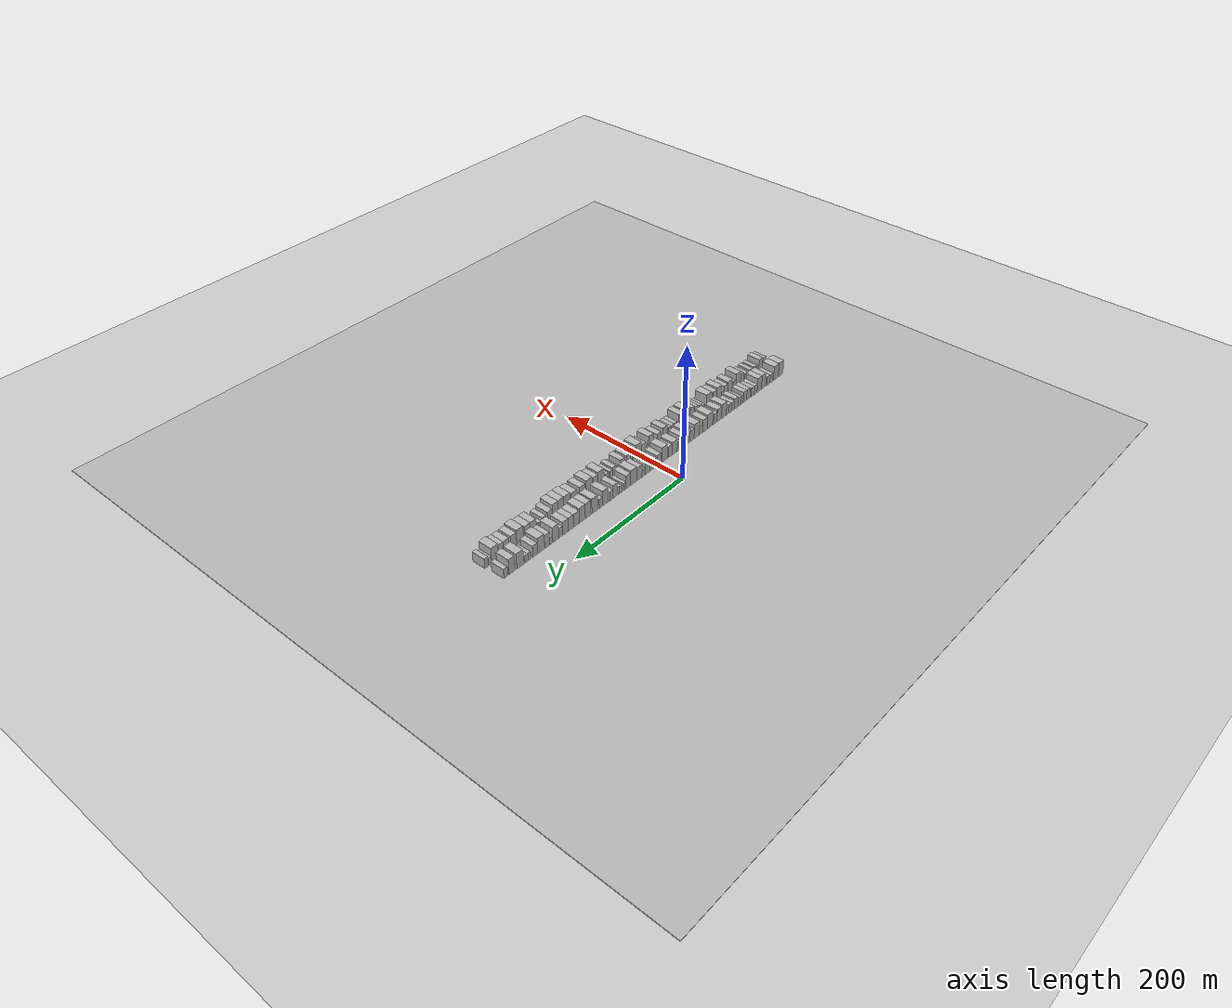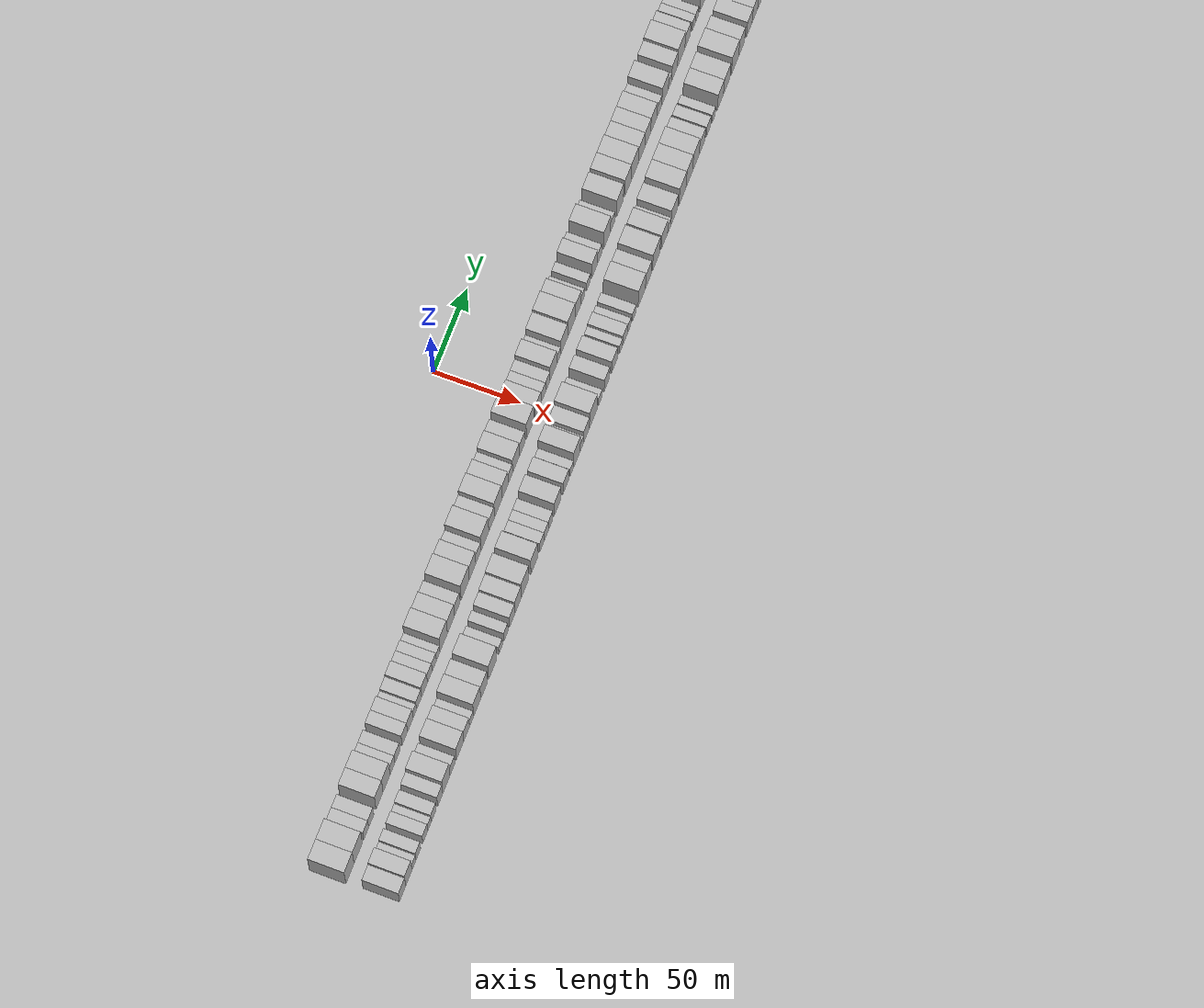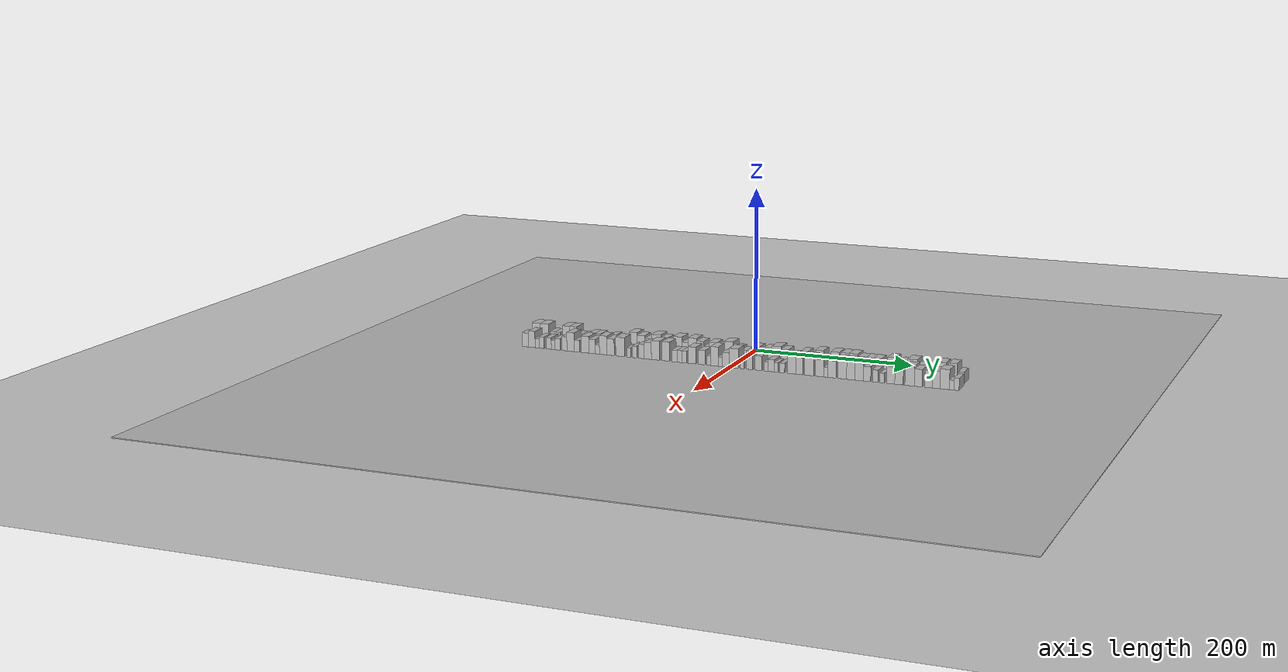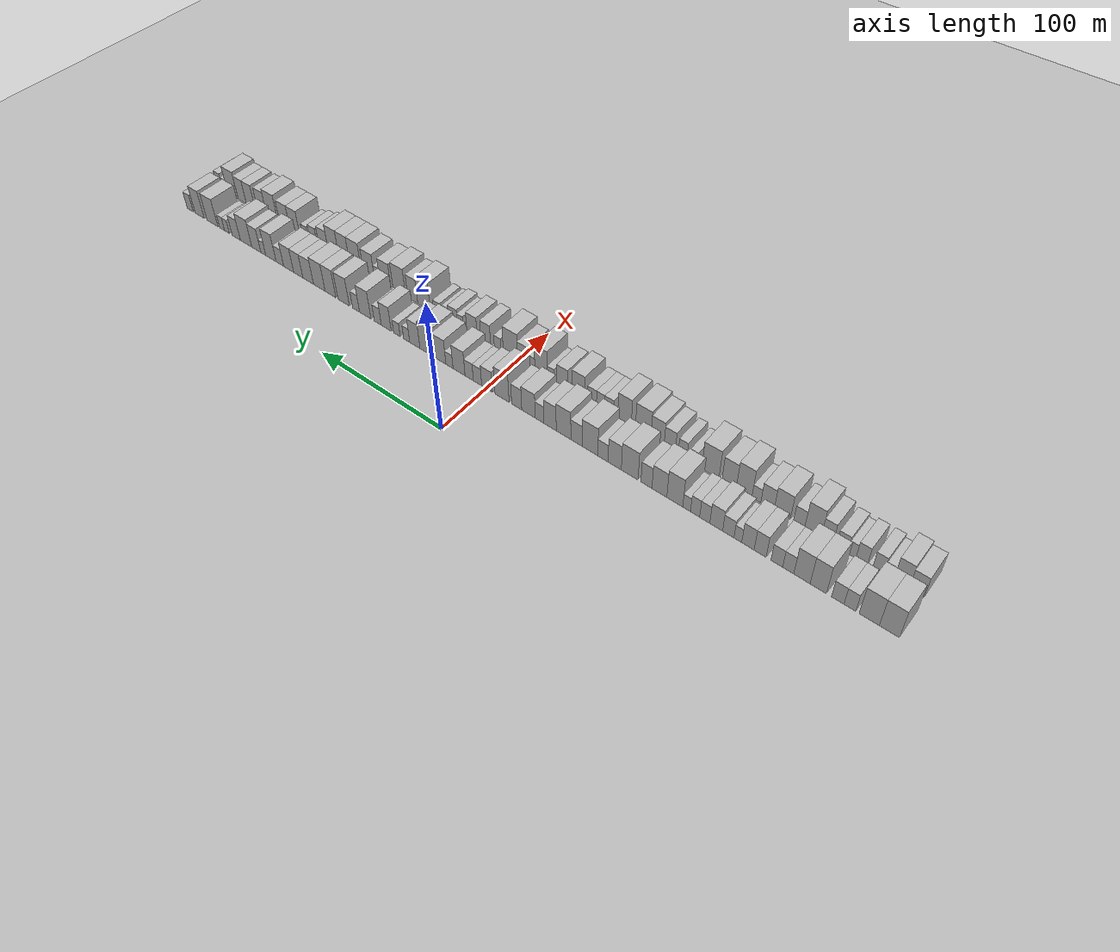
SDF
<?xml version="1.0" encoding="utf-8"?>

<sdf version="1.6">

   <world name="default">

      <gui fullscreen="0">

         <camera name="user_camera">

            <pose>-15 0 4.57585 0 0 0</pose>

            <view_controller>orbit</view_controller>

         </camera>

      </gui>

      <scene>

         <sky>

           <clouds>

             <speed>12</speed>

           </clouds>

         </sky>

         <ambient>0.4 0.4 0.4 1</ambient>

         <background>0.7 0.7 0.7 1</background>

         <shadows>1</shadows>

      </scene>

      <gravity>0 0 -9.8066</gravity>

      <magnetic_field>6e-06 2.3e-05 -4.2e-05</magnetic_field>

      <physics default="0" name="default_physics" type="ode">

         <ode>

            <solver>

               <type>quick</type>

               <iters>10</iters>

               <sor>1.0</sor>

               <use_dynamic_moi_rescaling>0</use_dynamic_moi_rescaling>

            </solver>

            <constraints>

               <cfm>0</cfm>

               <erp>0.2</erp>

               <contact_max_correcting_vel>100</contact_max_correcting_vel>

               <contact_surface_layer>0.001</contact_surface_layer>

            </constraints>

         </ode>

         <max_step_size>0.004</max_step_size>

         <real_time_factor>1</real_time_factor>

         <real_time_update_rate>250</real_time_update_rate>

      </physics>

      <light name="sun" type="directional">

         <cast_shadows>1</cast_shadows>

         <pose>0 0 10 0 0 0</pose>

         <diffuse>0.8 0.8 0.8 1</diffuse>

         <specular>0.2 0.2 0.2 1</specular>

         <attenuation>

            <range>1000</range>

            <constant>0.9</constant>

            <linear>0.01</linear>

            <quadratic>0.001</quadratic>

         </attenuation>

         <direction>-0.5 0.1 -0.9</direction>

      </light>

      <include>

         <name>ground_plane_1</name>

         <uri>model://HANNAS_ground_plane</uri>

         <pose>0 0 0  0 0 0</pose>

      </include>

      <include>

         <name>ground_plane_2</name>

         <uri>model://HANNAS_ground_plane</uri>

         <pose>100 0 0  0 0 0</pose>

      </include>

      <model name="building_1">

         <static>1</static>

         <pose frame="">50.0000 -270.3521 0 0.000000 0.000000 0.000000</pose>

         <link name="link">

            <pose frame="">0 0 12.00 0 0 0</pose>

            <collision name="collision">

               <geometry>

                  <box>

                     <size>20.0000 11.2958 24.0000</size>

                  </box>

               </geometry>

               <max_contacts>10</max_contacts>

               <surface>

                  <contact>

                     <ode/>

                  </contact>

                  <bounce/>

                  <friction>

                     <torsional>

                        <ode/>

                     </torsional>

                     <ode/>

                  </friction>

               </surface>

            </collision>

            <visual name="visual">

               <cast_shadows>0</cast_shadows>

               <geometry>

                  <box>

                     <size>20.0000 11.2958 24.0000</size>

                  </box>

               </geometry>

               <material>

                  <script>

                     <uri>model://HANNAS_wall/materials/scripts</uri>

                     <uri>model://HANNAS_wall/materials/textures</uri>

                     <name>vrc/HANNAS_wall</name>

                  </script>

               </material>

            </visual>

            <self_collide>0</self_collide>

            <enable_wind>0</enable_wind>

            <kinematic>0</kinematic>

         </link>

      </model>

      <model name="building_2">

         <static>1</static>

         <pose frame="">50.0000 -258.9503 0 0.000000 0.000000 0.000000</pose>

         <link name="link">

            <pose frame="">0 0 12.00 0 0 0</pose>

            <collision name="collision">

               <geometry>

                  <box>

                     <size>20.0000 11.5078 24.0000</size>

                  </box>

               </geometry>

               <max_contacts>10</max_contacts>

               <surface>

                  <contact>

                     <ode/>

                  </contact>

                  <bounce/>

                  <friction>

                     <torsional>

                        <ode/>

                     </torsional>

                     <ode/>

                  </friction>

               </surface>

            </collision>

            <visual name="visual">

               <cast_shadows>0</cast_shadows>

               <geometry>

                  <box>

                     <size>20.0000 11.5078 24.0000</size>

                  </box>

               </geometry>

               <material>

                  <script>

                     <uri>model://HANNAS_wall/materials/scripts</uri>

                     <uri>model://HANNAS_wall/materials/textures</uri>

                     <name>vrc/HANNAS_wall</name>

                  </script>

               </material>

            </visual>

            <self_collide>0</self_collide>

            <enable_wind>0</enable_wind>

            <kinematic>0</kinematic>

         </link>

      </model>

      <model name="building_3">

         <static>1</static>

         <pose frame="">50.0000 -247.7946 0 0.000000 0.000000 0.000000</pose>

         <link name="link">

            <pose frame="">0 0 7.50 0 0 0</pose>

            <collision name="collision">

               <geometry>

                  <box>

                     <size>20.0000 6.8036 15.0000</size>

                  </box>

               </geometry>

               <max_contacts>10</max_contacts>

               <surface>

                  <contact>

                     <ode/>

                  </contact>

                  <bounce/>

                  <friction>

                     <torsional>

                        <ode/>

                     </torsional>

                     <ode/>

                  </friction>

               </surface>

            </collision>

            <visual name="visual">

               <cast_shadows>0</cast_shadows>

               <geometry>

                  <box>

                     <size>20.0000 6.8036 15.0000</size>

                  </box>

               </geometry>

               <material>

                  <script>

                     <uri>model://HANNAS_wall/materials/scripts</uri>

                     <uri>model://HANNAS_wall/materials/textures</uri>

                     <name>vrc/HANNAS_wall</name>

                  </script>

               </material>

            </visual>

            <self_collide>0</self_collide>

            <enable_wind>0</enable_wind>

            <kinematic>0</kinematic>

         </link>

      </model>

      <model name="building_4">

         <static>1</static>

         <pose frame="">50.0000 -240.7317 0 0.000000 0.000000 0.000000</pose>

         <link name="link">

            <pose frame="">0 0 7.50 0 0 0</pose>

            <collision name="collision">

               <geometry>

                  <box>

                     <size>20.0000 7.3222 15.0000</size>

                  </box>

               </geometry>

               <max_contacts>10</max_contacts>

               <surface>

                  <contact>

                     <ode/>

                  </contact>

                  <bounce/>

                  <friction>

                     <torsional>

                        <ode/>

                     </torsional>

                     <ode/>

                  </friction>

               </surface>

            </collision>

            <visual name="visual">

               <cast_shadows>0</cast_shadows>

               <geometry>

                  <box>

                     <size>20.0000 7.3222 15.0000</size>

                  </box>

               </geometry>

               <material>

                  <script>

                     <uri>model://HANNAS_wall/materials/scripts</uri>

                     <uri>model://HANNAS_wall/materials/textures</uri>

                     <name>vrc/HANNAS_wall</name>

                  </script>

               </material>

            </visual>

            <self_collide>0</self_collide>

            <enable_wind>0</enable_wind>

            <kinematic>0</kinematic>

         </link>

      </model>

      <model name="building_5">

         <static>1</static>

         <pose frame="">50.0000 -229.2101 0 0.000000 0.000000 0.000000</pose>

         <link name="link">

            <pose frame="">0 0 12.00 0 0 0</pose>

            <collision name="collision">

               <geometry>

                  <box>

                     <size>20.0000 9.7211 24.0000</size>

                  </box>

               </geometry>

               <max_contacts>10</max_contacts>

               <surface>

                  <contact>

                     <ode/>

                  </contact>

                  <bounce/>

                  <friction>

                     <torsional>

                        <ode/>

                     </torsional>

                     <ode/>

                  </friction>

               </surface>

            </collision>

            <visual name="visual">

               <cast_shadows>0</cast_shadows>

               <geometry>

                  <box>

                     <size>20.0000 9.7211 24.0000</size>

                  </box>

               </geometry>

               <material>

                  <script>

                     <uri>model://HANNAS_wall/materials/scripts</uri>

                     <uri>model://HANNAS_wall/materials/textures</uri>

                     <name>vrc/HANNAS_wall</name>

                  </script>

               </material>

            </visual>

            <self_collide>0</self_collide>

            <enable_wind>0</enable_wind>

            <kinematic>0</kinematic>

         </link>

      </model>

      <model name="building_6">

         <static>1</static>

         <pose frame="">50.0000 -219.4116 0 0.000000 0.000000 0.000000</pose>

         <link name="link">

            <pose frame="">0 0 12.00 0 0 0</pose>

            <collision name="collision">

               <geometry>

                  <box>

                     <size>20.0000 9.8758 24.0000</size>

                  </box>

               </geometry>

               <max_contacts>10</max_contacts>

               <surface>

                  <contact>

                     <ode/>

                  </contact>

                  <bounce/>

                  <friction>

                     <torsional>

                        <ode/>

                     </torsional>

                     <ode/>

                  </friction>

               </surface>

            </collision>

            <visual name="visual">

               <cast_shadows>0</cast_shadows>

               <geometry>

                  <box>

                     <size>20.0000 9.8758 24.0000</size>

                  </box>

               </geometry>

               <material>

                  <script>

                     <uri>model://HANNAS_wall/materials/scripts</uri>

                     <uri>model://HANNAS_wall/materials/textures</uri>

                     <name>vrc/HANNAS_wall</name>

                  </script>

               </material>

            </visual>

            <self_collide>0</self_collide>

            <enable_wind>0</enable_wind>

            <kinematic>0</kinematic>

         </link>

      </model>

      <model name="building_7">

         <static>1</static>

         <pose frame="">50.0000 -211.0947 0 0.000000 0.000000 0.000000</pose>

         <link name="link">

            <pose frame="">0 0 7.50 0 0 0</pose>

            <collision name="collision">

               <geometry>

                  <box>

                     <size>20.0000 6.7581 15.0000</size>

                  </box>

               </geometry>

               <max_contacts>10</max_contacts>

               <surface>

                  <contact>

                     <ode/>

                  </contact>

                  <bounce/>

                  <friction>

                     <torsional>

                        <ode/>

                     </torsional>

                     <ode/>

                  </friction>

               </surface>

            </collision>

            <visual name="visual">

               <cast_shadows>0</cast_shadows>

               <geometry>

                  <box>

                     <size>20.0000 6.7581 15.0000</size>

                  </box>

               </geometry>

               <material>

                  <script>

                     <uri>model://HANNAS_wall/materials/scripts</uri>

                     <uri>model://HANNAS_wall/materials/textures</uri>

                     <name>vrc/HANNAS_wall</name>

                  </script>

               </material>

            </visual>

            <self_collide>0</self_collide>

            <enable_wind>0</enable_wind>

            <kinematic>0</kinematic>

         </link>

      </model>

      <model name="building_8">

         <static>1</static>

         <pose frame="">50.0000 -204.1174 0 0.000000 0.000000 0.000000</pose>

         <link name="link">

            <pose frame="">0 0 7.50 0 0 0</pose>

            <collision name="collision">

               <geometry>

                  <box>

                     <size>20.0000 7.1965 15.0000</size>

                  </box>

               </geometry>

               <max_contacts>10</max_contacts>

               <surface>

                  <contact>

                     <ode/>

                  </contact>

                  <bounce/>

                  <friction>

                     <torsional>

                        <ode/>

                     </torsional>

                     <ode/>

                  </friction>

               </surface>

            </collision>

            <visual name="visual">

               <cast_shadows>0</cast_shadows>

               <geometry>

                  <box>

                     <size>20.0000 7.1965 15.0000</size>

                  </box>

               </geometry>

               <material>

                  <script>

                     <uri>model://HANNAS_wall/materials/scripts</uri>

                     <uri>model://HANNAS_wall/materials/textures</uri>

                     <name>vrc/HANNAS_wall</name>

                  </script>

               </material>

            </visual>

            <self_collide>0</self_collide>

            <enable_wind>0</enable_wind>

            <kinematic>0</kinematic>

         </link>

      </model>

      <model name="building_9">

         <static>1</static>

         <pose frame="">50.0000 -193.7604 0 0.000000 0.000000 0.000000</pose>

         <link name="link">

            <pose frame="">0 0 9.00 0 0 0</pose>

            <collision name="collision">

               <geometry>

                  <box>

                     <size>20.0000 7.5175 18.0000</size>

                  </box>

               </geometry>

               <max_contacts>10</max_contacts>

               <surface>

                  <contact>

                     <ode/>

                  </contact>

                  <bounce/>

                  <friction>

                     <torsional>

                        <ode/>

                     </torsional>

                     <ode/>

                  </friction>

               </surface>

            </collision>

            <visual name="visual">

               <cast_shadows>0</cast_shadows>

               <geometry>

                  <box>

                     <size>20.0000 7.5175 18.0000</size>

                  </box>

               </geometry>

               <material>

                  <script>

                     <uri>model://HANNAS_wall/materials/scripts</uri>

                     <uri>model://HANNAS_wall/materials/textures</uri>

                     <name>vrc/HANNAS_wall</name>

                  </script>

               </material>

            </visual>

            <self_collide>0</self_collide>

            <enable_wind>0</enable_wind>

            <kinematic>0</kinematic>

         </link>

      </model>

      <model name="building_10">

         <static>1</static>

         <pose frame="">50.0000 -186.0805 0 0.000000 0.000000 0.000000</pose>

         <link name="link">

            <pose frame="">0 0 9.00 0 0 0</pose>

            <collision name="collision">

               <geometry>

                  <box>

                     <size>20.0000 7.8422 18.0000</size>

                  </box>

               </geometry>

               <max_contacts>10</max_contacts>

               <surface>

                  <contact>

                     <ode/>

                  </contact>

                  <bounce/>

                  <friction>

                     <torsional>

                        <ode/>

                     </torsional>

                     <ode/>

                  </friction>

               </surface>

            </collision>

            <visual name="visual">

               <cast_shadows>0</cast_shadows>

               <geometry>

                  <box>

                     <size>20.0000 7.8422 18.0000</size>

                  </box>

               </geometry>

               <material>

                  <script>

                     <uri>model://HANNAS_wall/materials/scripts</uri>

                     <uri>model://HANNAS_wall/materials/textures</uri>

                     <name>vrc/HANNAS_wall</name>

                  </script>

               </material>

            </visual>

            <self_collide>0</self_collide>

            <enable_wind>0</enable_wind>

            <kinematic>0</kinematic>

         </link>

      </model>

      <model name="building_11">

         <static>1</static>

         <pose frame="">50.0000 -179.7081 0 0.000000 0.000000 0.000000</pose>

         <link name="link">

            <pose frame="">0 0 6.00 0 0 0</pose>

            <collision name="collision">

               <geometry>

                  <box>

                     <size>20.0000 4.9028 12.0000</size>

                  </box>

               </geometry>

               <max_contacts>10</max_contacts>

               <surface>

                  <contact>

                     <ode/>

                  </contact>

                  <bounce/>

                  <friction>

                     <torsional>

                        <ode/>

                     </torsional>

                     <ode/>

                  </friction>

               </surface>

            </collision>

            <visual name="visual">

               <cast_shadows>0</cast_shadows>

               <geometry>

                  <box>

                     <size>20.0000 4.9028 12.0000</size>

                  </box>

               </geometry>

               <material>

                  <script>

                     <uri>model://HANNAS_wall/materials/scripts</uri>

                     <uri>model://HANNAS_wall/materials/textures</uri>

                     <name>vrc/HANNAS_wall</name>

                  </script>

               </material>

            </visual>

            <self_collide>0</self_collide>

            <enable_wind>0</enable_wind>

            <kinematic>0</kinematic>

         </link>

      </model>

      <model name="building_12">

         <static>1</static>

         <pose frame="">50.0000 -173.6037 0 0.000000 0.000000 0.000000</pose>

         <link name="link">

            <pose frame="">0 0 7.50 0 0 0</pose>

            <collision name="collision">

               <geometry>

                  <box>

                     <size>20.0000 7.3061 15.0000</size>

                  </box>

               </geometry>

               <max_contacts>10</max_contacts>

               <surface>

                  <contact>

                     <ode/>

                  </contact>

                  <bounce/>

                  <friction>

                     <torsional>

                        <ode/>

                     </torsional>

                     <ode/>

                  </friction>

               </surface>

            </collision>

            <visual name="visual">

               <cast_shadows>0</cast_shadows>

               <geometry>

                  <box>

                     <size>20.0000 7.3061 15.0000</size>

                  </box>

               </geometry>

               <material>

                  <script>

                     <uri>model://HANNAS_wall/materials/scripts</uri>

                     <uri>model://HANNAS_wall/materials/textures</uri>

                     <name>vrc/HANNAS_wall</name>

                  </script>

               </material>

            </visual>

            <self_collide>0</self_collide>

            <enable_wind>0</enable_wind>

            <kinematic>0</kinematic>

         </link>

      </model>

      <model name="building_13">

         <static>1</static>

         <pose frame="">50.0000 -165.8110 0 0.000000 0.000000 0.000000</pose>

         <link name="link">

            <pose frame="">0 0 9.00 0 0 0</pose>

            <collision name="collision">

               <geometry>

                  <box>

                     <size>20.0000 8.2792 18.0000</size>

                  </box>

               </geometry>

               <max_contacts>10</max_contacts>

               <surface>

                  <contact>

                     <ode/>

                  </contact>

                  <bounce/>

                  <friction>

                     <torsional>

                        <ode/>

                     </torsional>

                     <ode/>

                  </friction>

               </surface>

            </collision>

            <visual name="visual">

               <cast_shadows>0</cast_shadows>

               <geometry>

                  <box>

                     <size>20.0000 8.2792 18.0000</size>

                  </box>

               </geometry>

               <material>

                  <script>

                     <uri>model://HANNAS_wall/materials/scripts</uri>

                     <uri>model://HANNAS_wall/materials/textures</uri>

                     <name>vrc/HANNAS_wall</name>

                  </script>

               </material>

            </visual>

            <self_collide>0</self_collide>

            <enable_wind>0</enable_wind>

            <kinematic>0</kinematic>

         </link>

      </model>

      <model name="building_14">

         <static>1</static>

         <pose frame="">50.0000 -158.3307 0 0.000000 0.000000 0.000000</pose>

         <link name="link">

            <pose frame="">0 0 7.50 0 0 0</pose>

            <collision name="collision">

               <geometry>

                  <box>

                     <size>20.0000 6.6814 15.0000</size>

                  </box>

               </geometry>

               <max_contacts>10</max_contacts>

               <surface>

                  <contact>

                     <ode/>

                  </contact>

                  <bounce/>

                  <friction>

                     <torsional>

                        <ode/>

                     </torsional>

                     <ode/>

                  </friction>

               </surface>

            </collision>

            <visual name="visual">

               <cast_shadows>0</cast_shadows>

               <geometry>

                  <box>

                     <size>20.0000 6.6814 15.0000</size>

                  </box>

               </geometry>

               <material>

                  <script>

                     <uri>model://HANNAS_wall/materials/scripts</uri>

                     <uri>model://HANNAS_wall/materials/textures</uri>

                     <name>vrc/HANNAS_wall</name>

                  </script>

               </material>

            </visual>

            <self_collide>0</self_collide>

            <enable_wind>0</enable_wind>

            <kinematic>0</kinematic>

         </link>

      </model>

      <model name="building_15">

         <static>1</static>

         <pose frame="">50.0000 -151.9462 0 0.000000 0.000000 0.000000</pose>

         <link name="link">

            <pose frame="">0 0 7.50 0 0 0</pose>

            <collision name="collision">

               <geometry>

                  <box>

                     <size>20.0000 6.0876 15.0000</size>

                  </box>

               </geometry>

               <max_contacts>10</max_contacts>

               <surface>

                  <contact>

                     <ode/>

                  </contact>

                  <bounce/>

                  <friction>

                     <torsional>

                        <ode/>

                     </torsional>

                     <ode/>

                  </friction>

               </surface>

            </collision>

            <visual name="visual">

               <cast_shadows>0</cast_shadows>

               <geometry>

                  <box>

                     <size>20.0000 6.0876 15.0000</size>

                  </box>

               </geometry>

               <material>

                  <script>

                     <uri>model://HANNAS_wall/materials/scripts</uri>

                     <uri>model://HANNAS_wall/materials/textures</uri>

                     <name>vrc/HANNAS_wall</name>

                  </script>

               </material>

            </visual>

            <self_collide>0</self_collide>

            <enable_wind>0</enable_wind>

            <kinematic>0</kinematic>

         </link>

      </model>

      <model name="building_16">

         <static>1</static>

         <pose frame="">50.0000 -146.3313 0 0.000000 0.000000 0.000000</pose>

         <link name="link">

            <pose frame="">0 0 6.00 0 0 0</pose>

            <collision name="collision">

               <geometry>

                  <box>

                     <size>20.0000 5.1424 12.0000</size>

                  </box>

               </geometry>

               <max_contacts>10</max_contacts>

               <surface>

                  <contact>

                     <ode/>

                  </contact>

                  <bounce/>

                  <friction>

                     <torsional>

                        <ode/>

                     </torsional>

                     <ode/>

                  </friction>

               </surface>

            </collision>

            <visual name="visual">

               <cast_shadows>0</cast_shadows>

               <geometry>

                  <box>

                     <size>20.0000 5.1424 12.0000</size>

                  </box>

               </geometry>

               <material>

                  <script>

                     <uri>model://HANNAS_wall/materials/scripts</uri>

                     <uri>model://HANNAS_wall/materials/textures</uri>

                     <name>vrc/HANNAS_wall</name>

                  </script>

               </material>

            </visual>

            <self_collide>0</self_collide>

            <enable_wind>0</enable_wind>

            <kinematic>0</kinematic>

         </link>

      </model>

      <model name="building_17">

         <static>1</static>

         <pose frame="">50.0000 -138.4068 0 0.000000 0.000000 0.000000</pose>

         <link name="link">

            <pose frame="">0 0 12.00 0 0 0</pose>

            <collision name="collision">

               <geometry>

                  <box>

                     <size>20.0000 10.7065 24.0000</size>

                  </box>

               </geometry>

               <max_contacts>10</max_contacts>

               <surface>

                  <contact>

                     <ode/>

                  </contact>

                  <bounce/>

                  <friction>

                     <torsional>

                        <ode/>

                     </torsional>

                     <ode/>

                  </friction>

               </surface>

            </collision>

            <visual name="visual">

               <cast_shadows>0</cast_shadows>

               <geometry>

                  <box>

                     <size>20.0000 10.7065 24.0000</size>

                  </box>

               </geometry>

               <material>

                  <script>

                     <uri>model://HANNAS_wall/materials/scripts</uri>

                     <uri>model://HANNAS_wall/materials/textures</uri>

                     <name>vrc/HANNAS_wall</name>

                  </script>

               </material>

            </visual>

            <self_collide>0</self_collide>

            <enable_wind>0</enable_wind>

            <kinematic>0</kinematic>

         </link>

      </model>

      <model name="building_18">

         <static>1</static>

         <pose frame="">50.0000 -127.9700 0 0.000000 0.000000 0.000000</pose>

         <link name="link">

            <pose frame="">0 0 10.50 0 0 0</pose>

            <collision name="collision">

               <geometry>

                  <box>

                     <size>20.0000 10.1671 21.0000</size>

                  </box>

               </geometry>

               <max_contacts>10</max_contacts>

               <surface>

                  <contact>

                     <ode/>

                  </contact>

                  <bounce/>

                  <friction>

                     <torsional>

                        <ode/>

                     </torsional>

                     <ode/>

                  </friction>

               </surface>

            </collision>

            <visual name="visual">

               <cast_shadows>0</cast_shadows>

               <geometry>

                  <box>

                     <size>20.0000 10.1671 21.0000</size>

                  </box>

               </geometry>

               <material>

                  <script>

                     <uri>model://HANNAS_wall/materials/scripts</uri>

                     <uri>model://HANNAS_wall/materials/textures</uri>

                     <name>vrc/HANNAS_wall</name>

                  </script>

               </material>

            </visual>

            <self_collide>0</self_collide>

            <enable_wind>0</enable_wind>

            <kinematic>0</kinematic>

         </link>

      </model>

      <model name="building_19">

         <static>1</static>

         <pose frame="">50.0000 -119.1041 0 0.000000 0.000000 0.000000</pose>

         <link name="link">

            <pose frame="">0 0 9.00 0 0 0</pose>

            <collision name="collision">

               <geometry>

                  <box>

                     <size>20.0000 7.5647 18.0000</size>

                  </box>

               </geometry>

               <max_contacts>10</max_contacts>

               <surface>

                  <contact>

                     <ode/>

                  </contact>

                  <bounce/>

                  <friction>

                     <torsional>

                        <ode/>

                     </torsional>

                     <ode/>

                  </friction>

               </surface>

            </collision>

            <visual name="visual">

               <cast_shadows>0</cast_shadows>

               <geometry>

                  <box>

                     <size>20.0000 7.5647 18.0000</size>

                  </box>

               </geometry>

               <material>

                  <script>

                     <uri>model://HANNAS_wall/materials/scripts</uri>

                     <uri>model://HANNAS_wall/materials/textures</uri>

                     <name>vrc/HANNAS_wall</name>

                  </script>

               </material>

            </visual>

            <self_collide>0</self_collide>

            <enable_wind>0</enable_wind>

            <kinematic>0</kinematic>

         </link>

      </model>

      <model name="building_20">

         <static>1</static>

         <pose frame="">50.0000 -107.4591 0 0.000000 0.000000 0.000000</pose>

         <link name="link">

            <pose frame="">0 0 12.00 0 0 0</pose>

            <collision name="collision">

               <geometry>

                  <box>

                     <size>20.0000 11.7253 24.0000</size>

                  </box>

               </geometry>

               <max_contacts>10</max_contacts>

               <surface>

                  <contact>

                     <ode/>

                  </contact>

                  <bounce/>

                  <friction>

                     <torsional>

                        <ode/>

                     </torsional>

                     <ode/>

                  </friction>

               </surface>

            </collision>

            <visual name="visual">

               <cast_shadows>0</cast_shadows>

               <geometry>

                  <box>

                     <size>20.0000 11.7253 24.0000</size>

                  </box>

               </geometry>

               <material>

                  <script>

                     <uri>model://HANNAS_wall/materials/scripts</uri>

                     <uri>model://HANNAS_wall/materials/textures</uri>

                     <name>vrc/HANNAS_wall</name>

                  </script>

               </material>

            </visual>

            <self_collide>0</self_collide>

            <enable_wind>0</enable_wind>

            <kinematic>0</kinematic>

         </link>

      </model>

      <model name="building_21">

         <static>1</static>

         <pose frame="">50.0000 -96.9045 0 0.000000 0.000000 0.000000</pose>

         <link name="link">

            <pose frame="">0 0 10.50 0 0 0</pose>

            <collision name="collision">

               <geometry>

                  <box>

                     <size>20.0000 9.3840 21.0000</size>

                  </box>

               </geometry>

               <max_contacts>10</max_contacts>

               <surface>

                  <contact>

                     <ode/>

                  </contact>

                  <bounce/>

                  <friction>

                     <torsional>

                        <ode/>

                     </torsional>

                     <ode/>

                  </friction>

               </surface>

            </collision>

            <visual name="visual">

               <cast_shadows>0</cast_shadows>

               <geometry>

                  <box>

                     <size>20.0000 9.3840 21.0000</size>

                  </box>

               </geometry>

               <material>

                  <script>

                     <uri>model://HANNAS_wall/materials/scripts</uri>

                     <uri>model://HANNAS_wall/materials/textures</uri>

                     <name>vrc/HANNAS_wall</name>

                  </script>

               </material>

            </visual>

            <self_collide>0</self_collide>

            <enable_wind>0</enable_wind>

            <kinematic>0</kinematic>

         </link>

      </model>

      <model name="building_22">

         <static>1</static>

         <pose frame="">50.0000 -88.5318 0 0.000000 0.000000 0.000000</pose>

         <link name="link">

            <pose frame="">0 0 7.50 0 0 0</pose>

            <collision name="collision">

               <geometry>

                  <box>

                     <size>20.0000 7.3615 15.0000</size>

                  </box>

               </geometry>

               <max_contacts>10</max_contacts>

               <surface>

                  <contact>

                     <ode/>

                  </contact>

                  <bounce/>

                  <friction>

                     <torsional>

                        <ode/>

                     </torsional>

                     <ode/>

                  </friction>

               </surface>

            </collision>

            <visual name="visual">

               <cast_shadows>0</cast_shadows>

               <geometry>

                  <box>

                     <size>20.0000 7.3615 15.0000</size>

                  </box>

               </geometry>

               <material>

                  <script>

                     <uri>model://HANNAS_wall/materials/scripts</uri>

                     <uri>model://HANNAS_wall/materials/textures</uri>

                     <name>vrc/HANNAS_wall</name>

                  </script>

               </material>

            </visual>

            <self_collide>0</self_collide>

            <enable_wind>0</enable_wind>

            <kinematic>0</kinematic>

         </link>

      </model>

      <model name="building_23">

         <static>1</static>

         <pose frame="">50.0000 -79.0962 0 0.000000 0.000000 0.000000</pose>

         <link name="link">

            <pose frame="">0 0 12.00 0 0 0</pose>

            <collision name="collision">

               <geometry>

                  <box>

                     <size>20.0000 11.5096 24.0000</size>

                  </box>

               </geometry>

               <max_contacts>10</max_contacts>

               <surface>

                  <contact>

                     <ode/>

                  </contact>

                  <bounce/>

                  <friction>

                     <torsional>

                        <ode/>

                     </torsional>

                     <ode/>

                  </friction>

               </surface>

            </collision>

            <visual name="visual">

               <cast_shadows>0</cast_shadows>

               <geometry>

                  <box>

                     <size>20.0000 11.5096 24.0000</size>

                  </box>

               </geometry>

               <material>

                  <script>

                     <uri>model://HANNAS_wall/materials/scripts</uri>

                     <uri>model://HANNAS_wall/materials/textures</uri>

                     <name>vrc/HANNAS_wall</name>

                  </script>

               </material>

            </visual>

            <self_collide>0</self_collide>

            <enable_wind>0</enable_wind>

            <kinematic>0</kinematic>

         </link>

      </model>

      <model name="building_24">

         <static>1</static>

         <pose frame="">50.0000 -69.2204 0 0.000000 0.000000 0.000000</pose>

         <link name="link">

            <pose frame="">0 0 9.00 0 0 0</pose>

            <collision name="collision">

               <geometry>

                  <box>

                     <size>20.0000 8.2421 18.0000</size>

                  </box>

               </geometry>

               <max_contacts>10</max_contacts>

               <surface>

                  <contact>

                     <ode/>

                  </contact>

                  <bounce/>

                  <friction>

                     <torsional>

                        <ode/>

                     </torsional>

                     <ode/>

                  </friction>

               </surface>

            </collision>

            <visual name="visual">

               <cast_shadows>0</cast_shadows>

               <geometry>

                  <box>

                     <size>20.0000 8.2421 18.0000</size>

                  </box>

               </geometry>

               <material>

                  <script>

                     <uri>model://HANNAS_wall/materials/scripts</uri>

                     <uri>model://HANNAS_wall/materials/textures</uri>

                     <name>vrc/HANNAS_wall</name>

                  </script>

               </material>

            </visual>

            <self_collide>0</self_collide>

            <enable_wind>0</enable_wind>

            <kinematic>0</kinematic>

         </link>

      </model>

      <model name="building_25">

         <static>1</static>

         <pose frame="">50.0000 -59.6992 0 0.000000 0.000000 0.000000</pose>

         <link name="link">

            <pose frame="">0 0 12.00 0 0 0</pose>

            <collision name="collision">

               <geometry>

                  <box>

                     <size>20.0000 10.8002 24.0000</size>

                  </box>

               </geometry>

               <max_contacts>10</max_contacts>

               <surface>

                  <contact>

                     <ode/>

                  </contact>

                  <bounce/>

                  <friction>

                     <torsional>

                        <ode/>

                     </torsional>

                     <ode/>

                  </friction>

               </surface>

            </collision>

            <visual name="visual">

               <cast_shadows>0</cast_shadows>

               <geometry>

                  <box>

                     <size>20.0000 10.8002 24.0000</size>

                  </box>

               </geometry>

               <material>

                  <script>

                     <uri>model://HANNAS_wall/materials/scripts</uri>

                     <uri>model://HANNAS_wall/materials/textures</uri>

                     <name>vrc/HANNAS_wall</name>

                  </script>

               </material>

            </visual>

            <self_collide>0</self_collide>

            <enable_wind>0</enable_wind>

            <kinematic>0</kinematic>

         </link>

      </model>

      <model name="building_26">

         <static>1</static>

         <pose frame="">50.0000 -49.6911 0 0.000000 0.000000 0.000000</pose>

         <link name="link">

            <pose frame="">0 0 10.50 0 0 0</pose>

            <collision name="collision">

               <geometry>

                  <box>

                     <size>20.0000 9.2159 21.0000</size>

                  </box>

               </geometry>

               <max_contacts>10</max_contacts>

               <surface>

                  <contact>

                     <ode/>

                  </contact>

                  <bounce/>

                  <friction>

                     <torsional>

                        <ode/>

                     </torsional>

                     <ode/>

                  </friction>

               </surface>

            </collision>

            <visual name="visual">

               <cast_shadows>0</cast_shadows>

               <geometry>

                  <box>

                     <size>20.0000 9.2159 21.0000</size>

                  </box>

               </geometry>

               <material>

                  <script>

                     <uri>model://HANNAS_wall/materials/scripts</uri>

                     <uri>model://HANNAS_wall/materials/textures</uri>

                     <name>vrc/HANNAS_wall</name>

                  </script>

               </material>

            </visual>

            <self_collide>0</self_collide>

            <enable_wind>0</enable_wind>

            <kinematic>0</kinematic>

         </link>

      </model>

      <model name="building_27">

         <static>1</static>

         <pose frame="">50.0000 -41.7591 0 0.000000 0.000000 0.000000</pose>

         <link name="link">

            <pose frame="">0 0 7.50 0 0 0</pose>

            <collision name="collision">

               <geometry>

                  <box>

                     <size>20.0000 6.6481 15.0000</size>

                  </box>

               </geometry>

               <max_contacts>10</max_contacts>

               <surface>

                  <contact>

                     <ode/>

                  </contact>

                  <bounce/>

                  <friction>

                     <torsional>

                        <ode/>

                     </torsional>

                     <ode/>

                  </friction>

               </surface>

            </collision>

            <visual name="visual">

               <cast_shadows>0</cast_shadows>

               <geometry>

                  <box>

                     <size>20.0000 6.6481 15.0000</size>

                  </box>

               </geometry>

               <material>

                  <script>

                     <uri>model://HANNAS_wall/materials/scripts</uri>

                     <uri>model://HANNAS_wall/materials/textures</uri>

                     <name>vrc/HANNAS_wall</name>

                  </script>

               </material>

            </visual>

            <self_collide>0</self_collide>

            <enable_wind>0</enable_wind>

            <kinematic>0</kinematic>

         </link>

      </model>

      <model name="building_28">

         <static>1</static>

         <pose frame="">50.0000 -33.2414 0 0.000000 0.000000 0.000000</pose>

         <link name="link">

            <pose frame="">0 0 10.50 0 0 0</pose>

            <collision name="collision">

               <geometry>

                  <box>

                     <size>20.0000 10.3874 21.0000</size>

                  </box>

               </geometry>

               <max_contacts>10</max_contacts>

               <surface>

                  <contact>

                     <ode/>

                  </contact>

                  <bounce/>

                  <friction>

                     <torsional>

                        <ode/>

                     </torsional>

                     <ode/>

                  </friction>

               </surface>

            </collision>

            <visual name="visual">

               <cast_shadows>0</cast_shadows>

               <geometry>

                  <box>

                     <size>20.0000 10.3874 21.0000</size>

                  </box>

               </geometry>

               <material>

                  <script>

                     <uri>model://HANNAS_wall/materials/scripts</uri>

                     <uri>model://HANNAS_wall/materials/textures</uri>

                     <name>vrc/HANNAS_wall</name>

                  </script>

               </material>

            </visual>

            <self_collide>0</self_collide>

            <enable_wind>0</enable_wind>

            <kinematic>0</kinematic>

         </link>

      </model>

      <model name="building_29">

         <static>1</static>

         <pose frame="">50.0000 -24.1255 0 0.000000 0.000000 0.000000</pose>

         <link name="link">

            <pose frame="">0 0 9.00 0 0 0</pose>

            <collision name="collision">

               <geometry>

                  <box>

                     <size>20.0000 7.8444 18.0000</size>

                  </box>

               </geometry>

               <max_contacts>10</max_contacts>

               <surface>

                  <contact>

                     <ode/>

                  </contact>

                  <bounce/>

                  <friction>

                     <torsional>

                        <ode/>

                     </torsional>

                     <ode/>

                  </friction>

               </surface>

            </collision>

            <visual name="visual">

               <cast_shadows>0</cast_shadows>

               <geometry>

                  <box>

                     <size>20.0000 7.8444 18.0000</size>

                  </box>

               </geometry>

               <material>

                  <script>

                     <uri>model://HANNAS_wall/materials/scripts</uri>

                     <uri>model://HANNAS_wall/materials/textures</uri>

                     <name>vrc/HANNAS_wall</name>

                  </script>

               </material>

            </visual>

            <self_collide>0</self_collide>

            <enable_wind>0</enable_wind>

            <kinematic>0</kinematic>

         </link>

      </model>

      <model name="building_30">

         <static>1</static>

         <pose frame="">50.0000 -12.6385 0 0.000000 0.000000 0.000000</pose>

         <link name="link">

            <pose frame="">0 0 12.00 0 0 0</pose>

            <collision name="collision">

               <geometry>

                  <box>

                     <size>20.0000 11.1297 24.0000</size>

                  </box>

               </geometry>

               <max_contacts>10</max_contacts>

               <surface>

                  <contact>

                     <ode/>

                  </contact>

                  <bounce/>

                  <friction>

                     <torsional>

                        <ode/>

                     </torsional>

                     <ode/>

                  </friction>

               </surface>

            </collision>

            <visual name="visual">

               <cast_shadows>0</cast_shadows>

               <geometry>

                  <box>

                     <size>20.0000 11.1297 24.0000</size>

                  </box>

               </geometry>

               <material>

                  <script>

                     <uri>model://HANNAS_wall/materials/scripts</uri>

                     <uri>model://HANNAS_wall/materials/textures</uri>

                     <name>vrc/HANNAS_wall</name>

                  </script>

               </material>

            </visual>

            <self_collide>0</self_collide>

            <enable_wind>0</enable_wind>

            <kinematic>0</kinematic>

         </link>

      </model>

      <model name="building_31">

         <static>1</static>

         <pose frame="">50.0000 -0.7885 0 0.000000 0.000000 0.000000</pose>

         <link name="link">

            <pose frame="">0 0 9.00 0 0 0</pose>

            <collision name="collision">

               <geometry>

                  <box>

                     <size>20.0000 8.5702 18.0000</size>

                  </box>

               </geometry>

               <max_contacts>10</max_contacts>

               <surface>

                  <contact>

                     <ode/>

                  </contact>

                  <bounce/>

                  <friction>

                     <torsional>

                        <ode/>

                     </torsional>

                     <ode/>

                  </friction>

               </surface>

            </collision>

            <visual name="visual">

               <cast_shadows>0</cast_shadows>

               <geometry>

                  <box>

                     <size>20.0000 8.5702 18.0000</size>

                  </box>

               </geometry>

               <material>

                  <script>

                     <uri>model://HANNAS_wall/materials/scripts</uri>

                     <uri>model://HANNAS_wall/materials/textures</uri>

                     <name>vrc/HANNAS_wall</name>

                  </script>

               </material>

            </visual>

            <self_collide>0</self_collide>

            <enable_wind>0</enable_wind>

            <kinematic>0</kinematic>

         </link>

      </model>

      <model name="building_32">

         <static>1</static>

         <pose frame="">50.0000 6.8658 0 0.000000 0.000000 0.000000</pose>

         <link name="link">

            <pose frame="">0 0 7.50 0 0 0</pose>

            <collision name="collision">

               <geometry>

                  <box>

                     <size>20.0000 6.7384 15.0000</size>

                  </box>

               </geometry>

               <max_contacts>10</max_contacts>

               <surface>

                  <contact>

                     <ode/>

                  </contact>

                  <bounce/>

                  <friction>

                     <torsional>

                        <ode/>

                     </torsional>

                     <ode/>

                  </friction>

               </surface>

            </collision>

            <visual name="visual">

               <cast_shadows>0</cast_shadows>

               <geometry>

                  <box>

                     <size>20.0000 6.7384 15.0000</size>

                  </box>

               </geometry>

               <material>

                  <script>

                     <uri>model://HANNAS_wall/materials/scripts</uri>

                     <uri>model://HANNAS_wall/materials/textures</uri>

                     <name>vrc/HANNAS_wall</name>

                  </script>

               </material>

            </visual>

            <self_collide>0</self_collide>

            <enable_wind>0</enable_wind>

            <kinematic>0</kinematic>

         </link>

      </model>

      <model name="building_33">

         <static>1</static>

         <pose frame="">50.0000 13.6078 0 0.000000 0.000000 0.000000</pose>

         <link name="link">

            <pose frame="">0 0 7.50 0 0 0</pose>

            <collision name="collision">

               <geometry>

                  <box>

                     <size>20.0000 6.7456 15.0000</size>

                  </box>

               </geometry>

               <max_contacts>10</max_contacts>

               <surface>

                  <contact>

                     <ode/>

                  </contact>

                  <bounce/>

                  <friction>

                     <torsional>

                        <ode/>

                     </torsional>

                     <ode/>

                  </friction>

               </surface>

            </collision>

            <visual name="visual">

               <cast_shadows>0</cast_shadows>

               <geometry>

                  <box>

                     <size>20.0000 6.7456 15.0000</size>

                  </box>

               </geometry>

               <material>

                  <script>

                     <uri>model://HANNAS_wall/materials/scripts</uri>

                     <uri>model://HANNAS_wall/materials/textures</uri>

                     <name>vrc/HANNAS_wall</name>

                  </script>

               </material>

            </visual>

            <self_collide>0</self_collide>

            <enable_wind>0</enable_wind>

            <kinematic>0</kinematic>

         </link>

      </model>

      <model name="building_34">

         <static>1</static>

         <pose frame="">50.0000 21.9241 0 0.000000 0.000000 0.000000</pose>

         <link name="link">

            <pose frame="">0 0 10.50 0 0 0</pose>

            <collision name="collision">

               <geometry>

                  <box>

                     <size>20.0000 9.8871 21.0000</size>

                  </box>

               </geometry>

               <max_contacts>10</max_contacts>

               <surface>

                  <contact>

                     <ode/>

                  </contact>

                  <bounce/>

                  <friction>

                     <torsional>

                        <ode/>

                     </torsional>

                     <ode/>

                  </friction>

               </surface>

            </collision>

            <visual name="visual">

               <cast_shadows>0</cast_shadows>

               <geometry>

                  <box>

                     <size>20.0000 9.8871 21.0000</size>

                  </box>

               </geometry>

               <material>

                  <script>

                     <uri>model://HANNAS_wall/materials/scripts</uri>

                     <uri>model://HANNAS_wall/materials/textures</uri>

                     <name>vrc/HANNAS_wall</name>

                  </script>

               </material>

            </visual>

            <self_collide>0</self_collide>

            <enable_wind>0</enable_wind>

            <kinematic>0</kinematic>

         </link>

      </model>

      <model name="building_35">

         <static>1</static>

         <pose frame="">50.0000 29.8331 0 0.000000 0.000000 0.000000</pose>

         <link name="link">

            <pose frame="">0 0 6.00 0 0 0</pose>

            <collision name="collision">

               <geometry>

                  <box>

                     <size>20.0000 5.9308 12.0000</size>

                  </box>

               </geometry>

               <max_contacts>10</max_contacts>

               <surface>

                  <contact>

                     <ode/>

                  </contact>

                  <bounce/>

                  <friction>

                     <torsional>

                        <ode/>

                     </torsional>

                     <ode/>

                  </friction>

               </surface>

            </collision>

            <visual name="visual">

               <cast_shadows>0</cast_shadows>

               <geometry>

                  <box>

                     <size>20.0000 5.9308 12.0000</size>

                  </box>

               </geometry>

               <material>

                  <script>

                     <uri>model://HANNAS_wall/materials/scripts</uri>

                     <uri>model://HANNAS_wall/materials/textures</uri>

                     <name>vrc/HANNAS_wall</name>

                  </script>

               </material>

            </visual>

            <self_collide>0</self_collide>

            <enable_wind>0</enable_wind>

            <kinematic>0</kinematic>

         </link>

      </model>

      <model name="building_36">

         <static>1</static>

         <pose frame="">50.0000 37.9600 0 0.000000 0.000000 0.000000</pose>

         <link name="link">

            <pose frame="">0 0 10.50 0 0 0</pose>

            <collision name="collision">

               <geometry>

                  <box>

                     <size>20.0000 10.3231 21.0000</size>

                  </box>

               </geometry>

               <max_contacts>10</max_contacts>

               <surface>

                  <contact>

                     <ode/>

                  </contact>

                  <bounce/>

                  <friction>

                     <torsional>

                        <ode/>

                     </torsional>

                     <ode/>

                  </friction>

               </surface>

            </collision>

            <visual name="visual">

               <cast_shadows>0</cast_shadows>

               <geometry>

                  <box>

                     <size>20.0000 10.3231 21.0000</size>

                  </box>

               </geometry>

               <material>

                  <script>

                     <uri>model://HANNAS_wall/materials/scripts</uri>

                     <uri>model://HANNAS_wall/materials/textures</uri>

                     <name>vrc/HANNAS_wall</name>

                  </script>

               </material>

            </visual>

            <self_collide>0</self_collide>

            <enable_wind>0</enable_wind>

            <kinematic>0</kinematic>

         </link>

      </model>

      <model name="building_37">

         <static>1</static>

         <pose frame="">50.0000 48.8931 0 0.000000 0.000000 0.000000</pose>

         <link name="link">

            <pose frame="">0 0 12.00 0 0 0</pose>

            <collision name="collision">

               <geometry>

                  <box>

                     <size>20.0000 11.5431 24.0000</size>

                  </box>

               </geometry>

               <max_contacts>10</max_contacts>

               <surface>

                  <contact>

                     <ode/>

                  </contact>

                  <bounce/>

                  <friction>

                     <torsional>

                        <ode/>

                     </torsional>

                     <ode/>

                  </friction>

               </surface>

            </collision>

            <visual name="visual">

               <cast_shadows>0</cast_shadows>

               <geometry>

                  <box>

                     <size>20.0000 11.5431 24.0000</size>

                  </box>

               </geometry>

               <material>

                  <script>

                     <uri>model://HANNAS_wall/materials/scripts</uri>

                     <uri>model://HANNAS_wall/materials/textures</uri>

                     <name>vrc/HANNAS_wall</name>

                  </script>

               </material>

            </visual>

            <self_collide>0</self_collide>

            <enable_wind>0</enable_wind>

            <kinematic>0</kinematic>

         </link>

      </model>

      <model name="building_38">

         <static>1</static>

         <pose frame="">50.0000 59.0876 0 0.000000 0.000000 0.000000</pose>

         <link name="link">

            <pose frame="">0 0 10.50 0 0 0</pose>

            <collision name="collision">

               <geometry>

                  <box>

                     <size>20.0000 8.8458 21.0000</size>

                  </box>

               </geometry>

               <max_contacts>10</max_contacts>

               <surface>

                  <contact>

                     <ode/>

                  </contact>

                  <bounce/>

                  <friction>

                     <torsional>

                        <ode/>

                     </torsional>

                     <ode/>

                  </friction>

               </surface>

            </collision>

            <visual name="visual">

               <cast_shadows>0</cast_shadows>

               <geometry>

                  <box>

                     <size>20.0000 8.8458 21.0000</size>

                  </box>

               </geometry>

               <material>

                  <script>

                     <uri>model://HANNAS_wall/materials/scripts</uri>

                     <uri>model://HANNAS_wall/materials/textures</uri>

                     <name>vrc/HANNAS_wall</name>

                  </script>

               </material>

            </visual>

            <self_collide>0</self_collide>

            <enable_wind>0</enable_wind>

            <kinematic>0</kinematic>

         </link>

      </model>

      <model name="building_39">

         <static>1</static>

         <pose frame="">50.0000 66.1097 0 0.000000 0.000000 0.000000</pose>

         <link name="link">

            <pose frame="">0 0 6.00 0 0 0</pose>

            <collision name="collision">

               <geometry>

                  <box>

                     <size>20.0000 5.1983 12.0000</size>

                  </box>

               </geometry>

               <max_contacts>10</max_contacts>

               <surface>

                  <contact>

                     <ode/>

                  </contact>

                  <bounce/>

                  <friction>

                     <torsional>

                        <ode/>

                     </torsional>

                     <ode/>

                  </friction>

               </surface>

            </collision>

            <visual name="visual">

               <cast_shadows>0</cast_shadows>

               <geometry>

                  <box>

                     <size>20.0000 5.1983 12.0000</size>

                  </box>

               </geometry>

               <material>

                  <script>

                     <uri>model://HANNAS_wall/materials/scripts</uri>

                     <uri>model://HANNAS_wall/materials/textures</uri>

                     <name>vrc/HANNAS_wall</name>

                  </script>

               </material>

            </visual>

            <self_collide>0</self_collide>

            <enable_wind>0</enable_wind>

            <kinematic>0</kinematic>

         </link>

      </model>

      <model name="building_40">

         <static>1</static>

         <pose frame="">50.0000 74.5952 0 0.000000 0.000000 0.000000</pose>

         <link name="link">

            <pose frame="">0 0 6.00 0 0 0</pose>

            <collision name="collision">

               <geometry>

                  <box>

                     <size>20.0000 5.7728 12.0000</size>

                  </box>

               </geometry>

               <max_contacts>10</max_contacts>

               <surface>

                  <contact>

                     <ode/>

                  </contact>

                  <bounce/>

                  <friction>

                     <torsional>

                        <ode/>

                     </torsional>

                     <ode/>

                  </friction>

               </surface>

            </collision>

            <visual name="visual">

               <cast_shadows>0</cast_shadows>

               <geometry>

                  <box>

                     <size>20.0000 5.7728 12.0000</size>

                  </box>

               </geometry>

               <material>

                  <script>

                     <uri>model://HANNAS_wall/materials/scripts</uri>

                     <uri>model://HANNAS_wall/materials/textures</uri>

                     <name>vrc/HANNAS_wall</name>

                  </script>

               </material>

            </visual>

            <self_collide>0</self_collide>

            <enable_wind>0</enable_wind>

            <kinematic>0</kinematic>

         </link>

      </model>

      <model name="building_41">

         <static>1</static>

         <pose frame="">50.0000 83.8726 0 0.000000 0.000000 0.000000</pose>

         <link name="link">

            <pose frame="">0 0 10.50 0 0 0</pose>

            <collision name="collision">

               <geometry>

                  <box>

                     <size>20.0000 8.7820 21.0000</size>

                  </box>

               </geometry>

               <max_contacts>10</max_contacts>

               <surface>

                  <contact>

                     <ode/>

                  </contact>

                  <bounce/>

                  <friction>

                     <torsional>

                        <ode/>

                     </torsional>

                     <ode/>

                  </friction>

               </surface>

            </collision>

            <visual name="visual">

               <cast_shadows>0</cast_shadows>

               <geometry>

                  <box>

                     <size>20.0000 8.7820 21.0000</size>

                  </box>

               </geometry>

               <material>

                  <script>

                     <uri>model://HANNAS_wall/materials/scripts</uri>

                     <uri>model://HANNAS_wall/materials/textures</uri>

                     <name>vrc/HANNAS_wall</name>

                  </script>

               </material>

            </visual>

            <self_collide>0</self_collide>

            <enable_wind>0</enable_wind>

            <kinematic>0</kinematic>

         </link>

      </model>

      <model name="building_42">

         <static>1</static>

         <pose frame="">50.0000 91.4099 0 0.000000 0.000000 0.000000</pose>

         <link name="link">

            <pose frame="">0 0 7.50 0 0 0</pose>

            <collision name="collision">

               <geometry>

                  <box>

                     <size>20.0000 6.2925 15.0000</size>

                  </box>

               </geometry>

               <max_contacts>10</max_contacts>

               <surface>

                  <contact>

                     <ode/>

                  </contact>

                  <bounce/>

                  <friction>

                     <torsional>

                        <ode/>

                     </torsional>

                     <ode/>

                  </friction>

               </surface>

            </collision>

            <visual name="visual">

               <cast_shadows>0</cast_shadows>

               <geometry>

                  <box>

                     <size>20.0000 6.2925 15.0000</size>

                  </box>

               </geometry>

               <material>

                  <script>

                     <uri>model://HANNAS_wall/materials/scripts</uri>

                     <uri>model://HANNAS_wall/materials/textures</uri>

                     <name>vrc/HANNAS_wall</name>

                  </script>

               </material>

            </visual>

            <self_collide>0</self_collide>

            <enable_wind>0</enable_wind>

            <kinematic>0</kinematic>

         </link>

      </model>

      <model name="building_43">

         <static>1</static>

         <pose frame="">50.0000 102.6996 0 0.000000 0.000000 0.000000</pose>

         <link name="link">

            <pose frame="">0 0 12.00 0 0 0</pose>

            <collision name="collision">

               <geometry>

                  <box>

                     <size>20.0000 10.2869 24.0000</size>

                  </box>

               </geometry>

               <max_contacts>10</max_contacts>

               <surface>

                  <contact>

                     <ode/>

                  </contact>

                  <bounce/>

                  <friction>

                     <torsional>

                        <ode/>

                     </torsional>

                     <ode/>

                  </friction>

               </surface>

            </collision>

            <visual name="visual">

               <cast_shadows>0</cast_shadows>

               <geometry>

                  <box>

                     <size>20.0000 10.2869 24.0000</size>

                  </box>

               </geometry>

               <material>

                  <script>

                     <uri>model://HANNAS_wall/materials/scripts</uri>

                     <uri>model://HANNAS_wall/materials/textures</uri>

                     <name>vrc/HANNAS_wall</name>

                  </script>

               </material>

            </visual>

            <self_collide>0</self_collide>

            <enable_wind>0</enable_wind>

            <kinematic>0</kinematic>

         </link>

      </model>

      <model name="building_44">

         <static>1</static>

         <pose frame="">50.0000 110.9824 0 0.000000 0.000000 0.000000</pose>

         <link name="link">

            <pose frame="">0 0 7.50 0 0 0</pose>

            <collision name="collision">

               <geometry>

                  <box>

                     <size>20.0000 6.2788 15.0000</size>

                  </box>

               </geometry>

               <max_contacts>10</max_contacts>

               <surface>

                  <contact>

                     <ode/>

                  </contact>

                  <bounce/>

                  <friction>

                     <torsional>

                        <ode/>

                     </torsional>

                     <ode/>

                  </friction>

               </surface>

            </collision>

            <visual name="visual">

               <cast_shadows>0</cast_shadows>

               <geometry>

                  <box>

                     <size>20.0000 6.2788 15.0000</size>

                  </box>

               </geometry>

               <material>

                  <script>

                     <uri>model://HANNAS_wall/materials/scripts</uri>

                     <uri>model://HANNAS_wall/materials/textures</uri>

                     <name>vrc/HANNAS_wall</name>

                  </script>

               </material>

            </visual>

            <self_collide>0</self_collide>

            <enable_wind>0</enable_wind>

            <kinematic>0</kinematic>

         </link>

      </model>

      <model name="building_45">

         <static>1</static>

         <pose frame="">50.0000 122.3922 0 0.000000 0.000000 0.000000</pose>

         <link name="link">

            <pose frame="">0 0 12.00 0 0 0</pose>

            <collision name="collision">

               <geometry>

                  <box>

                     <size>20.0000 10.5407 24.0000</size>

                  </box>

               </geometry>

               <max_contacts>10</max_contacts>

               <surface>

                  <contact>

                     <ode/>

                  </contact>

                  <bounce/>

                  <friction>

                     <torsional>

                        <ode/>

                     </torsional>

                     <ode/>

                  </friction>

               </surface>

            </collision>

            <visual name="visual">

               <cast_shadows>0</cast_shadows>

               <geometry>

                  <box>

                     <size>20.0000 10.5407 24.0000</size>

                  </box>

               </geometry>

               <material>

                  <script>

                     <uri>model://HANNAS_wall/materials/scripts</uri>

                     <uri>model://HANNAS_wall/materials/textures</uri>

                     <name>vrc/HANNAS_wall</name>

                  </script>

               </material>

            </visual>

            <self_collide>0</self_collide>

            <enable_wind>0</enable_wind>

            <kinematic>0</kinematic>

         </link>

      </model>

      <model name="building_46">

         <static>1</static>

         <pose frame="">50.0000 134.6356 0 0.000000 0.000000 0.000000</pose>

         <link name="link">

            <pose frame="">0 0 12.00 0 0 0</pose>

            <collision name="collision">

               <geometry>

                  <box>

                     <size>20.0000 9.9462 24.0000</size>

                  </box>

               </geometry>

               <max_contacts>10</max_contacts>

               <surface>

                  <contact>

                     <ode/>

                  </contact>

                  <bounce/>

                  <friction>

                     <torsional>

                        <ode/>

                     </torsional>

                     <ode/>

                  </friction>

               </surface>

            </collision>

            <visual name="visual">

               <cast_shadows>0</cast_shadows>

               <geometry>

                  <box>

                     <size>20.0000 9.9462 24.0000</size>

                  </box>

               </geometry>

               <material>

                  <script>

                     <uri>model://HANNAS_wall/materials/scripts</uri>

                     <uri>model://HANNAS_wall/materials/textures</uri>

                     <name>vrc/HANNAS_wall</name>

                  </script>

               </material>

            </visual>

            <self_collide>0</self_collide>

            <enable_wind>0</enable_wind>

            <kinematic>0</kinematic>

         </link>

      </model>

      <model name="building_47">

         <static>1</static>

         <pose frame="">50.0000 145.1121 0 0.000000 0.000000 0.000000</pose>

         <link name="link">

            <pose frame="">0 0 12.00 0 0 0</pose>

            <collision name="collision">

               <geometry>

                  <box>

                     <size>20.0000 11.0066 24.0000</size>

                  </box>

               </geometry>

               <max_contacts>10</max_contacts>

               <surface>

                  <contact>

                     <ode/>

                  </contact>

                  <bounce/>

                  <friction>

                     <torsional>

                        <ode/>

                     </torsional>

                     <ode/>

                  </friction>

               </surface>

            </collision>

            <visual name="visual">

               <cast_shadows>0</cast_shadows>

               <geometry>

                  <box>

                     <size>20.0000 11.0066 24.0000</size>

                  </box>

               </geometry>

               <material>

                  <script>

                     <uri>model://HANNAS_wall/materials/scripts</uri>

                     <uri>model://HANNAS_wall/materials/textures</uri>

                     <name>vrc/HANNAS_wall</name>

                  </script>

               </material>

            </visual>

            <self_collide>0</self_collide>

            <enable_wind>0</enable_wind>

            <kinematic>0</kinematic>

         </link>

      </model>

      <model name="building_48">

         <static>1</static>

         <pose frame="">50.0000 155.7052 0 0.000000 0.000000 0.000000</pose>

         <link name="link">

            <pose frame="">0 0 10.50 0 0 0</pose>

            <collision name="collision">

               <geometry>

                  <box>

                     <size>20.0000 10.1797 21.0000</size>

                  </box>

               </geometry>

               <max_contacts>10</max_contacts>

               <surface>

                  <contact>

                     <ode/>

                  </contact>

                  <bounce/>

                  <friction>

                     <torsional>

                        <ode/>

                     </torsional>

                     <ode/>

                  </friction>

               </surface>

            </collision>

            <visual name="visual">

               <cast_shadows>0</cast_shadows>

               <geometry>

                  <box>

                     <size>20.0000 10.1797 21.0000</size>

                  </box>

               </geometry>

               <material>

                  <script>

                     <uri>model://HANNAS_wall/materials/scripts</uri>

                     <uri>model://HANNAS_wall/materials/textures</uri>

                     <name>vrc/HANNAS_wall</name>

                  </script>

               </material>

            </visual>

            <self_collide>0</self_collide>

            <enable_wind>0</enable_wind>

            <kinematic>0</kinematic>

         </link>

      </model>

      <model name="building_49">

         <static>1</static>

         <pose frame="">50.0000 165.2450 0 0.000000 0.000000 0.000000</pose>

         <link name="link">

            <pose frame="">0 0 10.50 0 0 0</pose>

            <collision name="collision">

               <geometry>

                  <box>

                     <size>20.0000 8.8998 21.0000</size>

                  </box>

               </geometry>

               <max_contacts>10</max_contacts>

               <surface>

                  <contact>

                     <ode/>

                  </contact>

                  <bounce/>

                  <friction>

                     <torsional>

                        <ode/>

                     </torsional>

                     <ode/>

                  </friction>

               </surface>

            </collision>

            <visual name="visual">

               <cast_shadows>0</cast_shadows>

               <geometry>

                  <box>

                     <size>20.0000 8.8998 21.0000</size>

                  </box>

               </geometry>

               <material>

                  <script>

                     <uri>model://HANNAS_wall/materials/scripts</uri>

                     <uri>model://HANNAS_wall/materials/textures</uri>

                     <name>vrc/HANNAS_wall</name>

                  </script>

               </material>

            </visual>

            <self_collide>0</self_collide>

            <enable_wind>0</enable_wind>

            <kinematic>0</kinematic>

         </link>

      </model>

      <model name="building_50">

         <static>1</static>

         <pose frame="">50.0000 174.5735 0 0.000000 0.000000 0.000000</pose>

         <link name="link">

            <pose frame="">0 0 10.50 0 0 0</pose>

            <collision name="collision">

               <geometry>

                  <box>

                     <size>20.0000 9.7571 21.0000</size>

                  </box>

               </geometry>

               <max_contacts>10</max_contacts>

               <surface>

                  <contact>

                     <ode/>

                  </contact>

                  <bounce/>

                  <friction>

                     <torsional>

                        <ode/>

                     </torsional>

                     <ode/>

                  </friction>

               </surface>

            </collision>

            <visual name="visual">

               <cast_shadows>0</cast_shadows>

               <geometry>

                  <box>

                     <size>20.0000 9.7571 21.0000</size>

                  </box>

               </geometry>

               <material>

                  <script>

                     <uri>model://HANNAS_wall/materials/scripts</uri>

                     <uri>model://HANNAS_wall/materials/textures</uri>

                     <name>vrc/HANNAS_wall</name>

                  </script>

               </material>

            </visual>

            <self_collide>0</self_collide>

            <enable_wind>0</enable_wind>

            <kinematic>0</kinematic>

         </link>

      </model>

      <model name="building_51">

         <static>1</static>

         <pose frame="">50.0000 183.1616 0 0.000000 0.000000 0.000000</pose>

         <link name="link">

            <pose frame="">0 0 7.50 0 0 0</pose>

            <collision name="collision">

               <geometry>

                  <box>

                     <size>20.0000 7.4192 15.0000</size>

                  </box>

               </geometry>

               <max_contacts>10</max_contacts>

               <surface>

                  <contact>

                     <ode/>

                  </contact>

                  <bounce/>

                  <friction>

                     <torsional>

                        <ode/>

                     </torsional>

                     <ode/>

                  </friction>

               </surface>

            </collision>

            <visual name="visual">

               <cast_shadows>0</cast_shadows>

               <geometry>

                  <box>

                     <size>20.0000 7.4192 15.0000</size>

                  </box>

               </geometry>

               <material>

                  <script>

                     <uri>model://HANNAS_wall/materials/scripts</uri>

                     <uri>model://HANNAS_wall/materials/textures</uri>

                     <name>vrc/HANNAS_wall</name>

                  </script>

               </material>

            </visual>

            <self_collide>0</self_collide>

            <enable_wind>0</enable_wind>

            <kinematic>0</kinematic>

         </link>

      </model>

      <model name="building_52">

         <static>1</static>

         <pose frame="">50.0000 192.0234 0 0.000000 0.000000 0.000000</pose>

         <link name="link">

            <pose frame="">0 0 12.00 0 0 0</pose>

            <collision name="collision">

               <geometry>

                  <box>

                     <size>20.0000 10.3044 24.0000</size>

                  </box>

               </geometry>

               <max_contacts>10</max_contacts>

               <surface>

                  <contact>

                     <ode/>

                  </contact>

                  <bounce/>

                  <friction>

                     <torsional>

                        <ode/>

                     </torsional>

                     <ode/>

                  </friction>

               </surface>

            </collision>

            <visual name="visual">

               <cast_shadows>0</cast_shadows>

               <geometry>

                  <box>

                     <size>20.0000 10.3044 24.0000</size>

                  </box>

               </geometry>

               <material>

                  <script>

                     <uri>model://HANNAS_wall/materials/scripts</uri>

                     <uri>model://HANNAS_wall/materials/textures</uri>

                     <name>vrc/HANNAS_wall</name>

                  </script>

               </material>

            </visual>

            <self_collide>0</self_collide>

            <enable_wind>0</enable_wind>

            <kinematic>0</kinematic>

         </link>

      </model>

      <model name="building_53">

         <static>1</static>

         <pose frame="">50.0000 199.6400 0 0.000000 0.000000 0.000000</pose>

         <link name="link">

            <pose frame="">0 0 6.00 0 0 0</pose>

            <collision name="collision">

               <geometry>

                  <box>

                     <size>20.0000 4.9287 12.0000</size>

                  </box>

               </geometry>

               <max_contacts>10</max_contacts>

               <surface>

                  <contact>

                     <ode/>

                  </contact>

                  <bounce/>

                  <friction>

                     <torsional>

                        <ode/>

                     </torsional>

                     <ode/>

                  </friction>

               </surface>

            </collision>

            <visual name="visual">

               <cast_shadows>0</cast_shadows>

               <geometry>

                  <box>

                     <size>20.0000 4.9287 12.0000</size>

                  </box>

               </geometry>

               <material>

                  <script>

                     <uri>model://HANNAS_wall/materials/scripts</uri>

                     <uri>model://HANNAS_wall/materials/textures</uri>

                     <name>vrc/HANNAS_wall</name>

                  </script>

               </material>

            </visual>

            <self_collide>0</self_collide>

            <enable_wind>0</enable_wind>

            <kinematic>0</kinematic>

         </link>

      </model>

      <model name="building_54">

         <static>1</static>

         <pose frame="">50.0000 206.6869 0 0.000000 0.000000 0.000000</pose>

         <link name="link">

            <pose frame="">0 0 10.50 0 0 0</pose>

            <collision name="collision">

               <geometry>

                  <box>

                     <size>20.0000 9.1651 21.0000</size>

                  </box>

               </geometry>

               <max_contacts>10</max_contacts>

               <surface>

                  <contact>

                     <ode/>

                  </contact>

                  <bounce/>

                  <friction>

                     <torsional>

                        <ode/>

                     </torsional>

                     <ode/>

                  </friction>

               </surface>

            </collision>

            <visual name="visual">

               <cast_shadows>0</cast_shadows>

               <geometry>

                  <box>

                     <size>20.0000 9.1651 21.0000</size>

                  </box>

               </geometry>

               <material>

                  <script>

                     <uri>model://HANNAS_wall/materials/scripts</uri>

                     <uri>model://HANNAS_wall/materials/textures</uri>

                     <name>vrc/HANNAS_wall</name>

                  </script>

               </material>

            </visual>

            <self_collide>0</self_collide>

            <enable_wind>0</enable_wind>

            <kinematic>0</kinematic>

         </link>

      </model>

      <model name="building_55">

         <static>1</static>

         <pose frame="">50.0000 217.1138 0 0.000000 0.000000 0.000000</pose>

         <link name="link">

            <pose frame="">0 0 12.00 0 0 0</pose>

            <collision name="collision">

               <geometry>

                  <box>

                     <size>20.0000 11.6887 24.0000</size>

                  </box>

               </geometry>

               <max_contacts>10</max_contacts>

               <surface>

                  <contact>

                     <ode/>

                  </contact>

                  <bounce/>

                  <friction>

                     <torsional>

                        <ode/>

                     </torsional>

                     <ode/>

                  </friction>

               </surface>

            </collision>

            <visual name="visual">

               <cast_shadows>0</cast_shadows>

               <geometry>

                  <box>

                     <size>20.0000 11.6887 24.0000</size>

                  </box>

               </geometry>

               <material>

                  <script>

                     <uri>model://HANNAS_wall/materials/scripts</uri>

                     <uri>model://HANNAS_wall/materials/textures</uri>

                     <name>vrc/HANNAS_wall</name>

                  </script>

               </material>

            </visual>

            <self_collide>0</self_collide>

            <enable_wind>0</enable_wind>

            <kinematic>0</kinematic>

         </link>

      </model>

      <model name="building_56">

         <static>1</static>

         <pose frame="">50.0000 227.1906 0 0.000000 0.000000 0.000000</pose>

         <link name="link">

            <pose frame="">0 0 9.00 0 0 0</pose>

            <collision name="collision">

               <geometry>

                  <box>

                     <size>20.0000 8.4649 18.0000</size>

                  </box>

               </geometry>

               <max_contacts>10</max_contacts>

               <surface>

                  <contact>

                     <ode/>

                  </contact>

                  <bounce/>

                  <friction>

                     <torsional>

                        <ode/>

                     </torsional>

                     <ode/>

                  </friction>

               </surface>

            </collision>

            <visual name="visual">

               <cast_shadows>0</cast_shadows>

               <geometry>

                  <box>

                     <size>20.0000 8.4649 18.0000</size>

                  </box>

               </geometry>

               <material>

                  <script>

                     <uri>model://HANNAS_wall/materials/scripts</uri>

                     <uri>model://HANNAS_wall/materials/textures</uri>

                     <name>vrc/HANNAS_wall</name>

                  </script>

               </material>

            </visual>

            <self_collide>0</self_collide>

            <enable_wind>0</enable_wind>

            <kinematic>0</kinematic>

         </link>

      </model>

      <model name="building_57">

         <static>1</static>

         <pose frame="">50.0000 236.9264 0 0.000000 0.000000 0.000000</pose>

         <link name="link">

            <pose frame="">0 0 6.00 0 0 0</pose>

            <collision name="collision">

               <geometry>

                  <box>

                     <size>20.0000 5.0067 12.0000</size>

                  </box>

               </geometry>

               <max_contacts>10</max_contacts>

               <surface>

                  <contact>

                     <ode/>

                  </contact>

                  <bounce/>

                  <friction>

                     <torsional>

                        <ode/>

                     </torsional>

                     <ode/>

                  </friction>

               </surface>

            </collision>

            <visual name="visual">

               <cast_shadows>0</cast_shadows>

               <geometry>

                  <box>

                     <size>20.0000 5.0067 12.0000</size>

                  </box>

               </geometry>

               <material>

                  <script>

                     <uri>model://HANNAS_wall/materials/scripts</uri>

                     <uri>model://HANNAS_wall/materials/textures</uri>

                     <name>vrc/HANNAS_wall</name>

                  </script>

               </material>

            </visual>

            <self_collide>0</self_collide>

            <enable_wind>0</enable_wind>

            <kinematic>0</kinematic>

         </link>

      </model>

      <model name="building_58">

         <static>1</static>

         <pose frame="">50.0000 241.9658 0 0.000000 0.000000 0.000000</pose>

         <link name="link">

            <pose frame="">0 0 6.00 0 0 0</pose>

            <collision name="collision">

               <geometry>

                  <box>

                     <size>20.0000 5.0721 12.0000</size>

                  </box>

               </geometry>

               <max_contacts>10</max_contacts>

               <surface>

                  <contact>

                     <ode/>

                  </contact>

                  <bounce/>

                  <friction>

                     <torsional>

                        <ode/>

                     </torsional>

                     <ode/>

                  </friction>

               </surface>

            </collision>

            <visual name="visual">

               <cast_shadows>0</cast_shadows>

               <geometry>

                  <box>

                     <size>20.0000 5.0721 12.0000</size>

                  </box>

               </geometry>

               <material>

                  <script>

                     <uri>model://HANNAS_wall/materials/scripts</uri>

                     <uri>model://HANNAS_wall/materials/textures</uri>

                     <name>vrc/HANNAS_wall</name>

                  </script>

               </material>

            </visual>

            <self_collide>0</self_collide>

            <enable_wind>0</enable_wind>

            <kinematic>0</kinematic>

         </link>

      </model>

      <model name="building_59">

         <static>1</static>

         <pose frame="">50.0000 252.2399 0 0.000000 0.000000 0.000000</pose>

         <link name="link">

            <pose frame="">0 0 12.00 0 0 0</pose>

            <collision name="collision">

               <geometry>

                  <box>

                     <size>20.0000 11.4761 24.0000</size>

                  </box>

               </geometry>

               <max_contacts>10</max_contacts>

               <surface>

                  <contact>

                     <ode/>

                  </contact>

                  <bounce/>

                  <friction>

                     <torsional>

                        <ode/>

                     </torsional>

                     <ode/>

                  </friction>

               </surface>

            </collision>

            <visual name="visual">

               <cast_shadows>0</cast_shadows>

               <geometry>

                  <box>

                     <size>20.0000 11.4761 24.0000</size>

                  </box>

               </geometry>

               <material>

                  <script>

                     <uri>model://HANNAS_wall/materials/scripts</uri>

                     <uri>model://HANNAS_wall/materials/textures</uri>

                     <name>vrc/HANNAS_wall</name>

                  </script>

               </material>

            </visual>

            <self_collide>0</self_collide>

            <enable_wind>0</enable_wind>

            <kinematic>0</kinematic>

         </link>

      </model>

      <model name="building_60">

         <static>1</static>

         <pose frame="">50.0000 265.8508 0 0.000000 0.000000 0.000000</pose>

         <link name="link">

            <pose frame="">0 0 12.00 0 0 0</pose>

            <collision name="collision">

               <geometry>

                  <box>

                     <size>20.0000 9.7458 24.0000</size>

                  </box>

               </geometry>

               <max_contacts>10</max_contacts>

               <surface>

                  <contact>

                     <ode/>

                  </contact>

                  <bounce/>

                  <friction>

                     <torsional>

                        <ode/>

                     </torsional>

                     <ode/>

                  </friction>

               </surface>

            </collision>

            <visual name="visual">

               <cast_shadows>0</cast_shadows>

               <geometry>

                  <box>

                     <size>20.0000 9.7458 24.0000</size>

                  </box>

               </geometry>

               <material>

                  <script>

                     <uri>model://HANNAS_wall/materials/scripts</uri>

                     <uri>model://HANNAS_wall/materials/textures</uri>

                     <name>vrc/HANNAS_wall</name>

                  </script>

               </material>

            </visual>

            <self_collide>0</self_collide>

            <enable_wind>0</enable_wind>

            <kinematic>0</kinematic>

         </link>

      </model>

      <model name="building_61">

         <static>1</static>

         <pose frame="">50.0000 275.9889 0 0.000000 0.000000 0.000000</pose>

         <link name="link">

            <pose frame="">0 0 7.50 0 0 0</pose>

            <collision name="collision">

               <geometry>

                  <box>

                     <size>20.0000 6.5304 15.0000</size>

                  </box>

               </geometry>

               <max_contacts>10</max_contacts>

               <surface>

                  <contact>

                     <ode/>

                  </contact>

                  <bounce/>

                  <friction>

                     <torsional>

                        <ode/>

                     </torsional>

                     <ode/>

                  </friction>

               </surface>

            </collision>

            <visual name="visual">

               <cast_shadows>0</cast_shadows>

               <geometry>

                  <box>

                     <size>20.0000 6.5304 15.0000</size>

                  </box>

               </geometry>

               <material>

                  <script>

                     <uri>model://HANNAS_wall/materials/scripts</uri>

                     <uri>model://HANNAS_wall/materials/textures</uri>

                     <name>vrc/HANNAS_wall</name>

                  </script>

               </material>

            </visual>

            <self_collide>0</self_collide>

            <enable_wind>0</enable_wind>

            <kinematic>0</kinematic>

         </link>

      </model>

      <model name="building_62">

         <static>1</static>

         <pose frame="">79.0000 -270.6561 0 0.000000 0.000000 0.000000</pose>

         <link name="link">

            <pose frame="">0 0 9.00 0 0 0</pose>

            <collision name="collision">

               <geometry>

                  <box>

                     <size>20.0000 8.6878 18.0000</size>

                  </box>

               </geometry>

               <max_contacts>10</max_contacts>

               <surface>

                  <contact>

                     <ode/>

                  </contact>

                  <bounce/>

                  <friction>

                     <torsional>

                        <ode/>

                     </torsional>

                     <ode/>

                  </friction>

               </surface>

            </collision>

            <visual name="visual">

               <cast_shadows>0</cast_shadows>

               <geometry>

                  <box>

                     <size>20.0000 8.6878 18.0000</size>

                  </box>

               </geometry>

               <material>

                  <script>

                     <uri>model://HANNAS_wall/materials/scripts</uri>

                     <uri>model://HANNAS_wall/materials/textures</uri>

                     <name>vrc/HANNAS_wall</name>

                  </script>

               </material>

            </visual>

            <self_collide>0</self_collide>

            <enable_wind>0</enable_wind>

            <kinematic>0</kinematic>

         </link>

      </model>

      <model name="building_63">

         <static>1</static>

         <pose frame="">79.0000 -261.8974 0 0.000000 0.000000 0.000000</pose>

         <link name="link">

            <pose frame="">0 0 10.50 0 0 0</pose>

            <collision name="collision">

               <geometry>

                  <box>

                     <size>20.0000 8.8296 21.0000</size>

                  </box>

               </geometry>

               <max_contacts>10</max_contacts>

               <surface>

                  <contact>

                     <ode/>

                  </contact>

                  <bounce/>

                  <friction>

                     <torsional>

                        <ode/>

                     </torsional>

                     <ode/>

                  </friction>

               </surface>

            </collision>

            <visual name="visual">

               <cast_shadows>0</cast_shadows>

               <geometry>

                  <box>

                     <size>20.0000 8.8296 21.0000</size>

                  </box>

               </geometry>

               <material>

                  <script>

                     <uri>model://HANNAS_wall/materials/scripts</uri>

                     <uri>model://HANNAS_wall/materials/textures</uri>

                     <name>vrc/HANNAS_wall</name>

                  </script>

               </material>

            </visual>

            <self_collide>0</self_collide>

            <enable_wind>0</enable_wind>

            <kinematic>0</kinematic>

         </link>

      </model>

      <model name="building_64">

         <static>1</static>

         <pose frame="">79.0000 -254.6926 0 0.000000 0.000000 0.000000</pose>

         <link name="link">

            <pose frame="">0 0 6.00 0 0 0</pose>

            <collision name="collision">

               <geometry>

                  <box>

                     <size>20.0000 5.5800 12.0000</size>

                  </box>

               </geometry>

               <max_contacts>10</max_contacts>

               <surface>

                  <contact>

                     <ode/>

                  </contact>

                  <bounce/>

                  <friction>

                     <torsional>

                        <ode/>

                     </torsional>

                     <ode/>

                  </friction>

               </surface>

            </collision>

            <visual name="visual">

               <cast_shadows>0</cast_shadows>

               <geometry>

                  <box>

                     <size>20.0000 5.5800 12.0000</size>

                  </box>

               </geometry>

               <material>

                  <script>

                     <uri>model://HANNAS_wall/materials/scripts</uri>

                     <uri>model://HANNAS_wall/materials/textures</uri>

                     <name>vrc/HANNAS_wall</name>

                  </script>

               </material>

            </visual>

            <self_collide>0</self_collide>

            <enable_wind>0</enable_wind>

            <kinematic>0</kinematic>

         </link>

      </model>

      <model name="building_65">

         <static>1</static>

         <pose frame="">79.0000 -248.5726 0 0.000000 0.000000 0.000000</pose>

         <link name="link">

            <pose frame="">0 0 7.50 0 0 0</pose>

            <collision name="collision">

               <geometry>

                  <box>

                     <size>20.0000 6.6600 15.0000</size>

                  </box>

               </geometry>

               <max_contacts>10</max_contacts>

               <surface>

                  <contact>

                     <ode/>

                  </contact>

                  <bounce/>

                  <friction>

                     <torsional>

                        <ode/>

                     </torsional>

                     <ode/>

                  </friction>

               </surface>

            </collision>

            <visual name="visual">

               <cast_shadows>0</cast_shadows>

               <geometry>

                  <box>

                     <size>20.0000 6.6600 15.0000</size>

                  </box>

               </geometry>

               <material>

                  <script>

                     <uri>model://HANNAS_wall/materials/scripts</uri>

                     <uri>model://HANNAS_wall/materials/textures</uri>

                     <name>vrc/HANNAS_wall</name>

                  </script>

               </material>

            </visual>

            <self_collide>0</self_collide>

            <enable_wind>0</enable_wind>

            <kinematic>0</kinematic>

         </link>

      </model>

      <model name="building_66">

         <static>1</static>

         <pose frame="">79.0000 -238.7857 0 0.000000 0.000000 0.000000</pose>

         <link name="link">

            <pose frame="">0 0 7.50 0 0 0</pose>

            <collision name="collision">

               <geometry>

                  <box>

                     <size>20.0000 6.9138 15.0000</size>

                  </box>

               </geometry>

               <max_contacts>10</max_contacts>

               <surface>

                  <contact>

                     <ode/>

                  </contact>

                  <bounce/>

                  <friction>

                     <torsional>

                        <ode/>

                     </torsional>

                     <ode/>

                  </friction>

               </surface>

            </collision>

            <visual name="visual">

               <cast_shadows>0</cast_shadows>

               <geometry>

                  <box>

                     <size>20.0000 6.9138 15.0000</size>

                  </box>

               </geometry>

               <material>

                  <script>

                     <uri>model://HANNAS_wall/materials/scripts</uri>

                     <uri>model://HANNAS_wall/materials/textures</uri>

                     <name>vrc/HANNAS_wall</name>

                  </script>

               </material>

            </visual>

            <self_collide>0</self_collide>

            <enable_wind>0</enable_wind>

            <kinematic>0</kinematic>

         </link>

      </model>

      <model name="building_67">

         <static>1</static>

         <pose frame="">79.0000 -232.8735 0 0.000000 0.000000 0.000000</pose>

         <link name="link">

            <pose frame="">0 0 6.00 0 0 0</pose>

            <collision name="collision">

               <geometry>

                  <box>

                     <size>20.0000 4.9106 12.0000</size>

                  </box>

               </geometry>

               <max_contacts>10</max_contacts>

               <surface>

                  <contact>

                     <ode/>

                  </contact>

                  <bounce/>

                  <friction>

                     <torsional>

                        <ode/>

                     </torsional>

                     <ode/>

                  </friction>

               </surface>

            </collision>

            <visual name="visual">

               <cast_shadows>0</cast_shadows>

               <geometry>

                  <box>

                     <size>20.0000 4.9106 12.0000</size>

                  </box>

               </geometry>

               <material>

                  <script>

                     <uri>model://HANNAS_wall/materials/scripts</uri>

                     <uri>model://HANNAS_wall/materials/textures</uri>

                     <name>vrc/HANNAS_wall</name>

                  </script>

               </material>

            </visual>

            <self_collide>0</self_collide>

            <enable_wind>0</enable_wind>

            <kinematic>0</kinematic>

         </link>

      </model>

      <model name="building_68">

         <static>1</static>

         <pose frame="">79.0000 -226.8763 0 0.000000 0.000000 0.000000</pose>

         <link name="link">

            <pose frame="">0 0 7.50 0 0 0</pose>

            <collision name="collision">

               <geometry>

                  <box>

                     <size>20.0000 7.0837 15.0000</size>

                  </box>

               </geometry>

               <max_contacts>10</max_contacts>

               <surface>

                  <contact>

                     <ode/>

                  </contact>

                  <bounce/>

                  <friction>

                     <torsional>

                        <ode/>

                     </torsional>

                     <ode/>

                  </friction>

               </surface>

            </collision>

            <visual name="visual">

               <cast_shadows>0</cast_shadows>

               <geometry>

                  <box>

                     <size>20.0000 7.0837 15.0000</size>

                  </box>

               </geometry>

               <material>

                  <script>

                     <uri>model://HANNAS_wall/materials/scripts</uri>

                     <uri>model://HANNAS_wall/materials/textures</uri>

                     <name>vrc/HANNAS_wall</name>

                  </script>

               </material>

            </visual>

            <self_collide>0</self_collide>

            <enable_wind>0</enable_wind>

            <kinematic>0</kinematic>

         </link>

      </model>

      <model name="building_69">

         <static>1</static>

         <pose frame="">79.0000 -217.7282 0 0.000000 0.000000 0.000000</pose>

         <link name="link">

            <pose frame="">0 0 9.00 0 0 0</pose>

            <collision name="collision">

               <geometry>

                  <box>

                     <size>20.0000 7.2126 18.0000</size>

                  </box>

               </geometry>

               <max_contacts>10</max_contacts>

               <surface>

                  <contact>

                     <ode/>

                  </contact>

                  <bounce/>

                  <friction>

                     <torsional>

                        <ode/>

                     </torsional>

                     <ode/>

                  </friction>

               </surface>

            </collision>

            <visual name="visual">

               <cast_shadows>0</cast_shadows>

               <geometry>

                  <box>

                     <size>20.0000 7.2126 18.0000</size>

                  </box>

               </geometry>

               <material>

                  <script>

                     <uri>model://HANNAS_wall/materials/scripts</uri>

                     <uri>model://HANNAS_wall/materials/textures</uri>

                     <name>vrc/HANNAS_wall</name>

                  </script>

               </material>

            </visual>

            <self_collide>0</self_collide>

            <enable_wind>0</enable_wind>

            <kinematic>0</kinematic>

         </link>

      </model>

      <model name="building_70">

         <static>1</static>

         <pose frame="">79.0000 -209.0349 0 0.000000 0.000000 0.000000</pose>

         <link name="link">

            <pose frame="">0 0 12.00 0 0 0</pose>

            <collision name="collision">

               <geometry>

                  <box>

                     <size>20.0000 10.1741 24.0000</size>

                  </box>

               </geometry>

               <max_contacts>10</max_contacts>

               <surface>

                  <contact>

                     <ode/>

                  </contact>

                  <bounce/>

                  <friction>

                     <torsional>

                        <ode/>

                     </torsional>

                     <ode/>

                  </friction>

               </surface>

            </collision>

            <visual name="visual">

               <cast_shadows>0</cast_shadows>

               <geometry>

                  <box>

                     <size>20.0000 10.1741 24.0000</size>

                  </box>

               </geometry>

               <material>

                  <script>

                     <uri>model://HANNAS_wall/materials/scripts</uri>

                     <uri>model://HANNAS_wall/materials/textures</uri>

                     <name>vrc/HANNAS_wall</name>

                  </script>

               </material>

            </visual>

            <self_collide>0</self_collide>

            <enable_wind>0</enable_wind>

            <kinematic>0</kinematic>

         </link>

      </model>

      <model name="building_71">

         <static>1</static>

         <pose frame="">79.0000 -200.4182 0 0.000000 0.000000 0.000000</pose>

         <link name="link">

            <pose frame="">0 0 7.50 0 0 0</pose>

            <collision name="collision">

               <geometry>

                  <box>

                     <size>20.0000 7.0592 15.0000</size>

                  </box>

               </geometry>

               <max_contacts>10</max_contacts>

               <surface>

                  <contact>

                     <ode/>

                  </contact>

                  <bounce/>

                  <friction>

                     <torsional>

                        <ode/>

                     </torsional>

                     <ode/>

                  </friction>

               </surface>

            </collision>

            <visual name="visual">

               <cast_shadows>0</cast_shadows>

               <geometry>

                  <box>

                     <size>20.0000 7.0592 15.0000</size>

                  </box>

               </geometry>

               <material>

                  <script>

                     <uri>model://HANNAS_wall/materials/scripts</uri>

                     <uri>model://HANNAS_wall/materials/textures</uri>

                     <name>vrc/HANNAS_wall</name>

                  </script>

               </material>

            </visual>

            <self_collide>0</self_collide>

            <enable_wind>0</enable_wind>

            <kinematic>0</kinematic>

         </link>

      </model>

      <model name="building_72">

         <static>1</static>

         <pose frame="">79.0000 -189.7333 0 0.000000 0.000000 0.000000</pose>

         <link name="link">

            <pose frame="">0 0 10.50 0 0 0</pose>

            <collision name="collision">

               <geometry>

                  <box>

                     <size>20.0000 10.3107 21.0000</size>

                  </box>

               </geometry>

               <max_contacts>10</max_contacts>

               <surface>

                  <contact>

                     <ode/>

                  </contact>

                  <bounce/>

                  <friction>

                     <torsional>

                        <ode/>

                     </torsional>

                     <ode/>

                  </friction>

               </surface>

            </collision>

            <visual name="visual">

               <cast_shadows>0</cast_shadows>

               <geometry>

                  <box>

                     <size>20.0000 10.3107 21.0000</size>

                  </box>

               </geometry>

               <material>

                  <script>

                     <uri>model://HANNAS_wall/materials/scripts</uri>

                     <uri>model://HANNAS_wall/materials/textures</uri>

                     <name>vrc/HANNAS_wall</name>

                  </script>

               </material>

            </visual>

            <self_collide>0</self_collide>

            <enable_wind>0</enable_wind>

            <kinematic>0</kinematic>

         </link>

      </model>

      <model name="building_73">

         <static>1</static>

         <pose frame="">79.0000 -180.3293 0 0.000000 0.000000 0.000000</pose>

         <link name="link">

            <pose frame="">0 0 9.00 0 0 0</pose>

            <collision name="collision">

               <geometry>

                  <box>

                     <size>20.0000 8.4972 18.0000</size>

                  </box>

               </geometry>

               <max_contacts>10</max_contacts>

               <surface>

                  <contact>

                     <ode/>

                  </contact>

                  <bounce/>

                  <friction>

                     <torsional>

                        <ode/>

                     </torsional>

                     <ode/>

                  </friction>

               </surface>

            </collision>

            <visual name="visual">

               <cast_shadows>0</cast_shadows>

               <geometry>

                  <box>

                     <size>20.0000 8.4972 18.0000</size>

                  </box>

               </geometry>

               <material>

                  <script>

                     <uri>model://HANNAS_wall/materials/scripts</uri>

                     <uri>model://HANNAS_wall/materials/textures</uri>

                     <name>vrc/HANNAS_wall</name>

                  </script>

               </material>

            </visual>

            <self_collide>0</self_collide>

            <enable_wind>0</enable_wind>

            <kinematic>0</kinematic>

         </link>

      </model>

      <model name="building_74">

         <static>1</static>

         <pose frame="">79.0000 -173.1874 0 0.000000 0.000000 0.000000</pose>

         <link name="link">

            <pose frame="">0 0 6.00 0 0 0</pose>

            <collision name="collision">

               <geometry>

                  <box>

                     <size>20.0000 5.7867 12.0000</size>

                  </box>

               </geometry>

               <max_contacts>10</max_contacts>

               <surface>

                  <contact>

                     <ode/>

                  </contact>

                  <bounce/>

                  <friction>

                     <torsional>

                        <ode/>

                     </torsional>

                     <ode/>

                  </friction>

               </surface>

            </collision>

            <visual name="visual">

               <cast_shadows>0</cast_shadows>

               <geometry>

                  <box>

                     <size>20.0000 5.7867 12.0000</size>

                  </box>

               </geometry>

               <material>

                  <script>

                     <uri>model://HANNAS_wall/materials/scripts</uri>

                     <uri>model://HANNAS_wall/materials/textures</uri>

                     <name>vrc/HANNAS_wall</name>

                  </script>

               </material>

            </visual>

            <self_collide>0</self_collide>

            <enable_wind>0</enable_wind>

            <kinematic>0</kinematic>

         </link>

      </model>

      <model name="building_75">

         <static>1</static>

         <pose frame="">79.0000 -165.1717 0 0.000000 0.000000 0.000000</pose>

         <link name="link">

            <pose frame="">0 0 12.00 0 0 0</pose>

            <collision name="collision">

               <geometry>

                  <box>

                     <size>20.0000 10.2445 24.0000</size>

                  </box>

               </geometry>

               <max_contacts>10</max_contacts>

               <surface>

                  <contact>

                     <ode/>

                  </contact>

                  <bounce/>

                  <friction>

                     <torsional>

                        <ode/>

                     </torsional>

                     <ode/>

                  </friction>

               </surface>

            </collision>

            <visual name="visual">

               <cast_shadows>0</cast_shadows>

               <geometry>

                  <box>

                     <size>20.0000 10.2445 24.0000</size>

                  </box>

               </geometry>

               <material>

                  <script>

                     <uri>model://HANNAS_wall/materials/scripts</uri>

                     <uri>model://HANNAS_wall/materials/textures</uri>

                     <name>vrc/HANNAS_wall</name>

                  </script>

               </material>

            </visual>

            <self_collide>0</self_collide>

            <enable_wind>0</enable_wind>

            <kinematic>0</kinematic>

         </link>

      </model>

      <model name="building_76">

         <static>1</static>

         <pose frame="">79.0000 -155.2880 0 0.000000 0.000000 0.000000</pose>

         <link name="link">

            <pose frame="">0 0 10.50 0 0 0</pose>

            <collision name="collision">

               <geometry>

                  <box>

                     <size>20.0000 9.5230 21.0000</size>

                  </box>

               </geometry>

               <max_contacts>10</max_contacts>

               <surface>

                  <contact>

                     <ode/>

                  </contact>

                  <bounce/>

                  <friction>

                     <torsional>

                        <ode/>

                     </torsional>

                     <ode/>

                  </friction>

               </surface>

            </collision>

            <visual name="visual">

               <cast_shadows>0</cast_shadows>

               <geometry>

                  <box>

                     <size>20.0000 9.5230 21.0000</size>

                  </box>

               </geometry>

               <material>

                  <script>

                     <uri>model://HANNAS_wall/materials/scripts</uri>

                     <uri>model://HANNAS_wall/materials/textures</uri>

                     <name>vrc/HANNAS_wall</name>

                  </script>

               </material>

            </visual>

            <self_collide>0</self_collide>

            <enable_wind>0</enable_wind>

            <kinematic>0</kinematic>

         </link>

      </model>

      <model name="building_77">

         <static>1</static>

         <pose frame="">79.0000 -142.7091 0 0.000000 0.000000 0.000000</pose>

         <link name="link">

            <pose frame="">0 0 12.00 0 0 0</pose>

            <collision name="collision">

               <geometry>

                  <box>

                     <size>20.0000 11.6348 24.0000</size>

                  </box>

               </geometry>

               <max_contacts>10</max_contacts>

               <surface>

                  <contact>

                     <ode/>

                  </contact>

                  <bounce/>

                  <friction>

                     <torsional>

                        <ode/>

                     </torsional>

                     <ode/>

                  </friction>

               </surface>

            </collision>

            <visual name="visual">

               <cast_shadows>0</cast_shadows>

               <geometry>

                  <box>

                     <size>20.0000 11.6348 24.0000</size>

                  </box>

               </geometry>

               <material>

                  <script>

                     <uri>model://HANNAS_wall/materials/scripts</uri>

                     <uri>model://HANNAS_wall/materials/textures</uri>

                     <name>vrc/HANNAS_wall</name>

                  </script>

               </material>

            </visual>

            <self_collide>0</self_collide>

            <enable_wind>0</enable_wind>

            <kinematic>0</kinematic>

         </link>

      </model>

      <model name="building_78">

         <static>1</static>

         <pose frame="">79.0000 -131.2579 0 0.000000 0.000000 0.000000</pose>

         <link name="link">

            <pose frame="">0 0 6.00 0 0 0</pose>

            <collision name="collision">

               <geometry>

                  <box>

                     <size>20.0000 5.2676 12.0000</size>

                  </box>

               </geometry>

               <max_contacts>10</max_contacts>

               <surface>

                  <contact>

                     <ode/>

                  </contact>

                  <bounce/>

                  <friction>

                     <torsional>

                        <ode/>

                     </torsional>

                     <ode/>

                  </friction>

               </surface>

            </collision>

            <visual name="visual">

               <cast_shadows>0</cast_shadows>

               <geometry>

                  <box>

                     <size>20.0000 5.2676 12.0000</size>

                  </box>

               </geometry>

               <material>

                  <script>

                     <uri>model://HANNAS_wall/materials/scripts</uri>

                     <uri>model://HANNAS_wall/materials/textures</uri>

                     <name>vrc/HANNAS_wall</name>

                  </script>

               </material>

            </visual>

            <self_collide>0</self_collide>

            <enable_wind>0</enable_wind>

            <kinematic>0</kinematic>

         </link>

      </model>

      <model name="building_79">

         <static>1</static>

         <pose frame="">79.0000 -123.6107 0 0.000000 0.000000 0.000000</pose>

         <link name="link">

            <pose frame="">0 0 7.50 0 0 0</pose>

            <collision name="collision">

               <geometry>

                  <box>

                     <size>20.0000 6.0268 15.0000</size>

                  </box>

               </geometry>

               <max_contacts>10</max_contacts>

               <surface>

                  <contact>

                     <ode/>

                  </contact>

                  <bounce/>

                  <friction>

                     <torsional>

                        <ode/>

                     </torsional>

                     <ode/>

                  </friction>

               </surface>

            </collision>

            <visual name="visual">

               <cast_shadows>0</cast_shadows>

               <geometry>

                  <box>

                     <size>20.0000 6.0268 15.0000</size>

                  </box>

               </geometry>

               <material>

                  <script>

                     <uri>model://HANNAS_wall/materials/scripts</uri>

                     <uri>model://HANNAS_wall/materials/textures</uri>

                     <name>vrc/HANNAS_wall</name>

                  </script>

               </material>

            </visual>

            <self_collide>0</self_collide>

            <enable_wind>0</enable_wind>

            <kinematic>0</kinematic>

         </link>

      </model>

      <model name="building_80">

         <static>1</static>

         <pose frame="">79.0000 -114.6585 0 0.000000 0.000000 0.000000</pose>

         <link name="link">

            <pose frame="">0 0 9.00 0 0 0</pose>

            <collision name="collision">

               <geometry>

                  <box>

                     <size>20.0000 7.8775 18.0000</size>

                  </box>

               </geometry>

               <max_contacts>10</max_contacts>

               <surface>

                  <contact>

                     <ode/>

                  </contact>

                  <bounce/>

                  <friction>

                     <torsional>

                        <ode/>

                     </torsional>

                     <ode/>

                  </friction>

               </surface>

            </collision>

            <visual name="visual">

               <cast_shadows>0</cast_shadows>

               <geometry>

                  <box>

                     <size>20.0000 7.8775 18.0000</size>

                  </box>

               </geometry>

               <material>

                  <script>

                     <uri>model://HANNAS_wall/materials/scripts</uri>

                     <uri>model://HANNAS_wall/materials/textures</uri>

                     <name>vrc/HANNAS_wall</name>

                  </script>

               </material>

            </visual>

            <self_collide>0</self_collide>

            <enable_wind>0</enable_wind>

            <kinematic>0</kinematic>

         </link>

      </model>

      <model name="building_81">

         <static>1</static>

         <pose frame="">79.0000 -106.0509 0 0.000000 0.000000 0.000000</pose>

         <link name="link">

            <pose frame="">0 0 10.50 0 0 0</pose>

            <collision name="collision">

               <geometry>

                  <box>

                     <size>20.0000 9.3377 21.0000</size>

                  </box>

               </geometry>

               <max_contacts>10</max_contacts>

               <surface>

                  <contact>

                     <ode/>

                  </contact>

                  <bounce/>

                  <friction>

                     <torsional>

                        <ode/>

                     </torsional>

                     <ode/>

                  </friction>

               </surface>

            </collision>

            <visual name="visual">

               <cast_shadows>0</cast_shadows>

               <geometry>

                  <box>

                     <size>20.0000 9.3377 21.0000</size>

                  </box>

               </geometry>

               <material>

                  <script>

                     <uri>model://HANNAS_wall/materials/scripts</uri>

                     <uri>model://HANNAS_wall/materials/textures</uri>

                     <name>vrc/HANNAS_wall</name>

                  </script>

               </material>

            </visual>

            <self_collide>0</self_collide>

            <enable_wind>0</enable_wind>

            <kinematic>0</kinematic>

         </link>

      </model>

      <model name="building_82">

         <static>1</static>

         <pose frame="">79.0000 -95.8247 0 0.000000 0.000000 0.000000</pose>

         <link name="link">

            <pose frame="">0 0 12.00 0 0 0</pose>

            <collision name="collision">

               <geometry>

                  <box>

                     <size>20.0000 11.1148 24.0000</size>

                  </box>

               </geometry>

               <max_contacts>10</max_contacts>

               <surface>

                  <contact>

                     <ode/>

                  </contact>

                  <bounce/>

                  <friction>

                     <torsional>

                        <ode/>

                     </torsional>

                     <ode/>

                  </friction>

               </surface>

            </collision>

            <visual name="visual">

               <cast_shadows>0</cast_shadows>

               <geometry>

                  <box>

                     <size>20.0000 11.1148 24.0000</size>

                  </box>

               </geometry>

               <material>

                  <script>

                     <uri>model://HANNAS_wall/materials/scripts</uri>

                     <uri>model://HANNAS_wall/materials/textures</uri>

                     <name>vrc/HANNAS_wall</name>

                  </script>

               </material>

            </visual>

            <self_collide>0</self_collide>

            <enable_wind>0</enable_wind>

            <kinematic>0</kinematic>

         </link>

      </model>

      <model name="building_83">

         <static>1</static>

         <pose frame="">79.0000 -82.3069 0 0.000000 0.000000 0.000000</pose>

         <link name="link">

            <pose frame="">0 0 12.00 0 0 0</pose>

            <collision name="collision">

               <geometry>

                  <box>

                     <size>20.0000 9.9207 24.0000</size>

                  </box>

               </geometry>

               <max_contacts>10</max_contacts>

               <surface>

                  <contact>

                     <ode/>

                  </contact>

                  <bounce/>

                  <friction>

                     <torsional>

                        <ode/>

                     </torsional>

                     <ode/>

                  </friction>

               </surface>

            </collision>

            <visual name="visual">

               <cast_shadows>0</cast_shadows>

               <geometry>

                  <box>

                     <size>20.0000 9.9207 24.0000</size>

                  </box>

               </geometry>

               <material>

                  <script>

                     <uri>model://HANNAS_wall/materials/scripts</uri>

                     <uri>model://HANNAS_wall/materials/textures</uri>

                     <name>vrc/HANNAS_wall</name>

                  </script>

               </material>

            </visual>

            <self_collide>0</self_collide>

            <enable_wind>0</enable_wind>

            <kinematic>0</kinematic>

         </link>

      </model>

      <model name="building_84">

         <static>1</static>

         <pose frame="">79.0000 -71.0695 0 0.000000 0.000000 0.000000</pose>

         <link name="link">

            <pose frame="">0 0 7.50 0 0 0</pose>

            <collision name="collision">

               <geometry>

                  <box>

                     <size>20.0000 6.5541 15.0000</size>

                  </box>

               </geometry>

               <max_contacts>10</max_contacts>

               <surface>

                  <contact>

                     <ode/>

                  </contact>

                  <bounce/>

                  <friction>

                     <torsional>

                        <ode/>

                     </torsional>

                     <ode/>

                  </friction>

               </surface>

            </collision>

            <visual name="visual">

               <cast_shadows>0</cast_shadows>

               <geometry>

                  <box>

                     <size>20.0000 6.5541 15.0000</size>

                  </box>

               </geometry>

               <material>

                  <script>

                     <uri>model://HANNAS_wall/materials/scripts</uri>

                     <uri>model://HANNAS_wall/materials/textures</uri>

                     <name>vrc/HANNAS_wall</name>

                  </script>

               </material>

            </visual>

            <self_collide>0</self_collide>

            <enable_wind>0</enable_wind>

            <kinematic>0</kinematic>

         </link>

      </model>

      <model name="building_85">

         <static>1</static>

         <pose frame="">79.0000 -64.7242 0 0.000000 0.000000 0.000000</pose>

         <link name="link">

            <pose frame="">0 0 7.50 0 0 0</pose>

            <collision name="collision">

               <geometry>

                  <box>

                     <size>20.0000 6.1364 15.0000</size>

                  </box>

               </geometry>

               <max_contacts>10</max_contacts>

               <surface>

                  <contact>

                     <ode/>

                  </contact>

                  <bounce/>

                  <friction>

                     <torsional>

                        <ode/>

                     </torsional>

                     <ode/>

                  </friction>

               </surface>

            </collision>

            <visual name="visual">

               <cast_shadows>0</cast_shadows>

               <geometry>

                  <box>

                     <size>20.0000 6.1364 15.0000</size>

                  </box>

               </geometry>

               <material>

                  <script>

                     <uri>model://HANNAS_wall/materials/scripts</uri>

                     <uri>model://HANNAS_wall/materials/textures</uri>

                     <name>vrc/HANNAS_wall</name>

                  </script>

               </material>

            </visual>

            <self_collide>0</self_collide>

            <enable_wind>0</enable_wind>

            <kinematic>0</kinematic>

         </link>

      </model>

      <model name="building_86">

         <static>1</static>

         <pose frame="">79.0000 -58.3399 0 0.000000 0.000000 0.000000</pose>

         <link name="link">

            <pose frame="">0 0 7.50 0 0 0</pose>

            <collision name="collision">

               <geometry>

                  <box>

                     <size>20.0000 6.6323 15.0000</size>

                  </box>

               </geometry>

               <max_contacts>10</max_contacts>

               <surface>

                  <contact>

                     <ode/>

                  </contact>

                  <bounce/>

                  <friction>

                     <torsional>

                        <ode/>

                     </torsional>

                     <ode/>

                  </friction>

               </surface>

            </collision>

            <visual name="visual">

               <cast_shadows>0</cast_shadows>

               <geometry>

                  <box>

                     <size>20.0000 6.6323 15.0000</size>

                  </box>

               </geometry>

               <material>

                  <script>

                     <uri>model://HANNAS_wall/materials/scripts</uri>

                     <uri>model://HANNAS_wall/materials/textures</uri>

                     <name>vrc/HANNAS_wall</name>

                  </script>

               </material>

            </visual>

            <self_collide>0</self_collide>

            <enable_wind>0</enable_wind>

            <kinematic>0</kinematic>

         </link>

      </model>

      <model name="building_87">

         <static>1</static>

         <pose frame="">79.0000 -48.0432 0 0.000000 0.000000 0.000000</pose>

         <link name="link">

            <pose frame="">0 0 10.50 0 0 0</pose>

            <collision name="collision">

               <geometry>

                  <box>

                     <size>20.0000 9.9612 21.0000</size>

                  </box>

               </geometry>

               <max_contacts>10</max_contacts>

               <surface>

                  <contact>

                     <ode/>

                  </contact>

                  <bounce/>

                  <friction>

                     <torsional>

                        <ode/>

                     </torsional>

                     <ode/>

                  </friction>

               </surface>

            </collision>

            <visual name="visual">

               <cast_shadows>0</cast_shadows>

               <geometry>

                  <box>

                     <size>20.0000 9.9612 21.0000</size>

                  </box>

               </geometry>

               <material>

                  <script>

                     <uri>model://HANNAS_wall/materials/scripts</uri>

                     <uri>model://HANNAS_wall/materials/textures</uri>

                     <name>vrc/HANNAS_wall</name>

                  </script>

               </material>

            </visual>

            <self_collide>0</self_collide>

            <enable_wind>0</enable_wind>

            <kinematic>0</kinematic>

         </link>

      </model>

      <model name="building_88">

         <static>1</static>

         <pose frame="">79.0000 -35.7702 0 0.000000 0.000000 0.000000</pose>

         <link name="link">

            <pose frame="">0 0 9.00 0 0 0</pose>

            <collision name="collision">

               <geometry>

                  <box>

                     <size>20.0000 8.5848 18.0000</size>

                  </box>

               </geometry>

               <max_contacts>10</max_contacts>

               <surface>

                  <contact>

                     <ode/>

                  </contact>

                  <bounce/>

                  <friction>

                     <torsional>

                        <ode/>

                     </torsional>

                     <ode/>

                  </friction>

               </surface>

            </collision>

            <visual name="visual">

               <cast_shadows>0</cast_shadows>

               <geometry>

                  <box>

                     <size>20.0000 8.5848 18.0000</size>

                  </box>

               </geometry>

               <material>

                  <script>

                     <uri>model://HANNAS_wall/materials/scripts</uri>

                     <uri>model://HANNAS_wall/materials/textures</uri>

                     <name>vrc/HANNAS_wall</name>

                  </script>

               </material>

            </visual>

            <self_collide>0</self_collide>

            <enable_wind>0</enable_wind>

            <kinematic>0</kinematic>

         </link>

      </model>

      <model name="building_89">

         <static>1</static>

         <pose frame="">79.0000 -26.8504 0 0.000000 0.000000 0.000000</pose>

         <link name="link">

            <pose frame="">0 0 6.00 0 0 0</pose>

            <collision name="collision">

               <geometry>

                  <box>

                     <size>20.0000 5.2548 12.0000</size>

                  </box>

               </geometry>

               <max_contacts>10</max_contacts>

               <surface>

                  <contact>

                     <ode/>

                  </contact>

                  <bounce/>

                  <friction>

                     <torsional>

                        <ode/>

                     </torsional>

                     <ode/>

                  </friction>

               </surface>

            </collision>

            <visual name="visual">

               <cast_shadows>0</cast_shadows>

               <geometry>

                  <box>

                     <size>20.0000 5.2548 12.0000</size>

                  </box>

               </geometry>

               <material>

                  <script>

                     <uri>model://HANNAS_wall/materials/scripts</uri>

                     <uri>model://HANNAS_wall/materials/textures</uri>

                     <name>vrc/HANNAS_wall</name>

                  </script>

               </material>

            </visual>

            <self_collide>0</self_collide>

            <enable_wind>0</enable_wind>

            <kinematic>0</kinematic>

         </link>

      </model>

      <model name="building_90">

         <static>1</static>

         <pose frame="">79.0000 -19.2862 0 0.000000 0.000000 0.000000</pose>

         <link name="link">

            <pose frame="">0 0 12.00 0 0 0</pose>

            <collision name="collision">

               <geometry>

                  <box>

                     <size>20.0000 9.8735 24.0000</size>

                  </box>

               </geometry>

               <max_contacts>10</max_contacts>

               <surface>

                  <contact>

                     <ode/>

                  </contact>

                  <bounce/>

                  <friction>

                     <torsional>

                        <ode/>

                     </torsional>

                     <ode/>

                  </friction>

               </surface>

            </collision>

            <visual name="visual">

               <cast_shadows>0</cast_shadows>

               <geometry>

                  <box>

                     <size>20.0000 9.8735 24.0000</size>

                  </box>

               </geometry>

               <material>

                  <script>

                     <uri>model://HANNAS_wall/materials/scripts</uri>

                     <uri>model://HANNAS_wall/materials/textures</uri>

                     <name>vrc/HANNAS_wall</name>

                  </script>

               </material>

            </visual>

            <self_collide>0</self_collide>

            <enable_wind>0</enable_wind>

            <kinematic>0</kinematic>

         </link>

      </model>

      <model name="building_91">

         <static>1</static>

         <pose frame="">79.0000 -11.9008 0 0.000000 0.000000 0.000000</pose>

         <link name="link">

            <pose frame="">0 0 6.00 0 0 0</pose>

            <collision name="collision">

               <geometry>

                  <box>

                     <size>20.0000 4.8973 12.0000</size>

                  </box>

               </geometry>

               <max_contacts>10</max_contacts>

               <surface>

                  <contact>

                     <ode/>

                  </contact>

                  <bounce/>

                  <friction>

                     <torsional>

                        <ode/>

                     </torsional>

                     <ode/>

                  </friction>

               </surface>

            </collision>

            <visual name="visual">

               <cast_shadows>0</cast_shadows>

               <geometry>

                  <box>

                     <size>20.0000 4.8973 12.0000</size>

                  </box>

               </geometry>

               <material>

                  <script>

                     <uri>model://HANNAS_wall/materials/scripts</uri>

                     <uri>model://HANNAS_wall/materials/textures</uri>

                     <name>vrc/HANNAS_wall</name>

                  </script>

               </material>

            </visual>

            <self_collide>0</self_collide>

            <enable_wind>0</enable_wind>

            <kinematic>0</kinematic>

         </link>

      </model>

      <model name="building_92">

         <static>1</static>

         <pose frame="">79.0000 -5.0426 0 0.000000 0.000000 0.000000</pose>

         <link name="link">

            <pose frame="">0 0 9.00 0 0 0</pose>

            <collision name="collision">

               <geometry>

                  <box>

                     <size>20.0000 8.8192 18.0000</size>

                  </box>

               </geometry>

               <max_contacts>10</max_contacts>

               <surface>

                  <contact>

                     <ode/>

                  </contact>

                  <bounce/>

                  <friction>

                     <torsional>

                        <ode/>

                     </torsional>

                     <ode/>

                  </friction>

               </surface>

            </collision>

            <visual name="visual">

               <cast_shadows>0</cast_shadows>

               <geometry>

                  <box>

                     <size>20.0000 8.8192 18.0000</size>

                  </box>

               </geometry>

               <material>

                  <script>

                     <uri>model://HANNAS_wall/materials/scripts</uri>

                     <uri>model://HANNAS_wall/materials/textures</uri>

                     <name>vrc/HANNAS_wall</name>

                  </script>

               </material>

            </visual>

            <self_collide>0</self_collide>

            <enable_wind>0</enable_wind>

            <kinematic>0</kinematic>

         </link>

      </model>

      <model name="building_93">

         <static>1</static>

         <pose frame="">79.0000 5.1922 0 0.000000 0.000000 0.000000</pose>

         <link name="link">

            <pose frame="">0 0 12.00 0 0 0</pose>

            <collision name="collision">

               <geometry>

                  <box>

                     <size>20.0000 11.6505 24.0000</size>

                  </box>

               </geometry>

               <max_contacts>10</max_contacts>

               <surface>

                  <contact>

                     <ode/>

                  </contact>

                  <bounce/>

                  <friction>

                     <torsional>

                        <ode/>

                     </torsional>

                     <ode/>

                  </friction>

               </surface>

            </collision>

            <visual name="visual">

               <cast_shadows>0</cast_shadows>

               <geometry>

                  <box>

                     <size>20.0000 11.6505 24.0000</size>

                  </box>

               </geometry>

               <material>

                  <script>

                     <uri>model://HANNAS_wall/materials/scripts</uri>

                     <uri>model://HANNAS_wall/materials/textures</uri>

                     <name>vrc/HANNAS_wall</name>

                  </script>

               </material>

            </visual>

            <self_collide>0</self_collide>

            <enable_wind>0</enable_wind>

            <kinematic>0</kinematic>

         </link>

      </model>

      <model name="building_94">

         <static>1</static>

         <pose frame="">79.0000 15.7318 0 0.000000 0.000000 0.000000</pose>

         <link name="link">

            <pose frame="">0 0 6.00 0 0 0</pose>

            <collision name="collision">

               <geometry>

                  <box>

                     <size>20.0000 5.4286 12.0000</size>

                  </box>

               </geometry>

               <max_contacts>10</max_contacts>

               <surface>

                  <contact>

                     <ode/>

                  </contact>

                  <bounce/>

                  <friction>

                     <torsional>

                        <ode/>

                     </torsional>

                     <ode/>

                  </friction>

               </surface>

            </collision>

            <visual name="visual">

               <cast_shadows>0</cast_shadows>

               <geometry>

                  <box>

                     <size>20.0000 5.4286 12.0000</size>

                  </box>

               </geometry>

               <material>

                  <script>

                     <uri>model://HANNAS_wall/materials/scripts</uri>

                     <uri>model://HANNAS_wall/materials/textures</uri>

                     <name>vrc/HANNAS_wall</name>

                  </script>

               </material>

            </visual>

            <self_collide>0</self_collide>

            <enable_wind>0</enable_wind>

            <kinematic>0</kinematic>

         </link>

      </model>

      <model name="building_95">

         <static>1</static>

         <pose frame="">79.0000 25.4994 0 0.000000 0.000000 0.000000</pose>

         <link name="link">

            <pose frame="">0 0 9.00 0 0 0</pose>

            <collision name="collision">

               <geometry>

                  <box>

                     <size>20.0000 8.1065 18.0000</size>

                  </box>

               </geometry>

               <max_contacts>10</max_contacts>

               <surface>

                  <contact>

                     <ode/>

                  </contact>

                  <bounce/>

                  <friction>

                     <torsional>

                        <ode/>

                     </torsional>

                     <ode/>

                  </friction>

               </surface>

            </collision>

            <visual name="visual">

               <cast_shadows>0</cast_shadows>

               <geometry>

                  <box>

                     <size>20.0000 8.1065 18.0000</size>

                  </box>

               </geometry>

               <material>

                  <script>

                     <uri>model://HANNAS_wall/materials/scripts</uri>

                     <uri>model://HANNAS_wall/materials/textures</uri>

                     <name>vrc/HANNAS_wall</name>

                  </script>

               </material>

            </visual>

            <self_collide>0</self_collide>

            <enable_wind>0</enable_wind>

            <kinematic>0</kinematic>

         </link>

      </model>

      <model name="building_96">

         <static>1</static>

         <pose frame="">79.0000 36.9092 0 0.000000 0.000000 0.000000</pose>

         <link name="link">

            <pose frame="">0 0 9.00 0 0 0</pose>

            <collision name="collision">

               <geometry>

                  <box>

                     <size>20.0000 8.7132 18.0000</size>

                  </box>

               </geometry>

               <max_contacts>10</max_contacts>

               <surface>

                  <contact>

                     <ode/>

                  </contact>

                  <bounce/>

                  <friction>

                     <torsional>

                        <ode/>

                     </torsional>

                     <ode/>

                  </friction>

               </surface>

            </collision>

            <visual name="visual">

               <cast_shadows>0</cast_shadows>

               <geometry>

                  <box>

                     <size>20.0000 8.7132 18.0000</size>

                  </box>

               </geometry>

               <material>

                  <script>

                     <uri>model://HANNAS_wall/materials/scripts</uri>

                     <uri>model://HANNAS_wall/materials/textures</uri>

                     <name>vrc/HANNAS_wall</name>

                  </script>

               </material>

            </visual>

            <self_collide>0</self_collide>

            <enable_wind>0</enable_wind>

            <kinematic>0</kinematic>

         </link>

      </model>

      <model name="building_97">

         <static>1</static>

         <pose frame="">79.0000 46.7136 0 0.000000 0.000000 0.000000</pose>

         <link name="link">

            <pose frame="">0 0 6.00 0 0 0</pose>

            <collision name="collision">

               <geometry>

                  <box>

                     <size>20.0000 4.8956 12.0000</size>

                  </box>

               </geometry>

               <max_contacts>10</max_contacts>

               <surface>

                  <contact>

                     <ode/>

                  </contact>

                  <bounce/>

                  <friction>

                     <torsional>

                        <ode/>

                     </torsional>

                     <ode/>

                  </friction>

               </surface>

            </collision>

            <visual name="visual">

               <cast_shadows>0</cast_shadows>

               <geometry>

                  <box>

                     <size>20.0000 4.8956 12.0000</size>

                  </box>

               </geometry>

               <material>

                  <script>

                     <uri>model://HANNAS_wall/materials/scripts</uri>

                     <uri>model://HANNAS_wall/materials/textures</uri>

                     <name>vrc/HANNAS_wall</name>

                  </script>

               </material>

            </visual>

            <self_collide>0</self_collide>

            <enable_wind>0</enable_wind>

            <kinematic>0</kinematic>

         </link>

      </model>

      <model name="building_98">

         <static>1</static>

         <pose frame="">79.0000 52.9090 0 0.000000 0.000000 0.000000</pose>

         <link name="link">

            <pose frame="">0 0 7.50 0 0 0</pose>

            <collision name="collision">

               <geometry>

                  <box>

                     <size>20.0000 7.4953 15.0000</size>

                  </box>

               </geometry>

               <max_contacts>10</max_contacts>

               <surface>

                  <contact>

                     <ode/>

                  </contact>

                  <bounce/>

                  <friction>

                     <torsional>

                        <ode/>

                     </torsional>

                     <ode/>

                  </friction>

               </surface>

            </collision>

            <visual name="visual">

               <cast_shadows>0</cast_shadows>

               <geometry>

                  <box>

                     <size>20.0000 7.4953 15.0000</size>

                  </box>

               </geometry>

               <material>

                  <script>

                     <uri>model://HANNAS_wall/materials/scripts</uri>

                     <uri>model://HANNAS_wall/materials/textures</uri>

                     <name>vrc/HANNAS_wall</name>

                  </script>

               </material>

            </visual>

            <self_collide>0</self_collide>

            <enable_wind>0</enable_wind>

            <kinematic>0</kinematic>

         </link>

      </model>

      <model name="building_99">

         <static>1</static>

         <pose frame="">79.0000 59.2433 0 0.000000 0.000000 0.000000</pose>

         <link name="link">

            <pose frame="">0 0 6.00 0 0 0</pose>

            <collision name="collision">

               <geometry>

                  <box>

                     <size>20.0000 5.1733 12.0000</size>

                  </box>

               </geometry>

               <max_contacts>10</max_contacts>

               <surface>

                  <contact>

                     <ode/>

                  </contact>

                  <bounce/>

                  <friction>

                     <torsional>

                        <ode/>

                     </torsional>

                     <ode/>

                  </friction>

               </surface>

            </collision>

            <visual name="visual">

               <cast_shadows>0</cast_shadows>

               <geometry>

                  <box>

                     <size>20.0000 5.1733 12.0000</size>

                  </box>

               </geometry>

               <material>

                  <script>

                     <uri>model://HANNAS_wall/materials/scripts</uri>

                     <uri>model://HANNAS_wall/materials/textures</uri>

                     <name>vrc/HANNAS_wall</name>

                  </script>

               </material>

            </visual>

            <self_collide>0</self_collide>

            <enable_wind>0</enable_wind>

            <kinematic>0</kinematic>

         </link>

      </model>

      <model name="building_100">

         <static>1</static>

         <pose frame="">79.0000 66.7829 0 0.000000 0.000000 0.000000</pose>

         <link name="link">

            <pose frame="">0 0 6.00 0 0 0</pose>

            <collision name="collision">

               <geometry>

                  <box>

                     <size>20.0000 5.9058 12.0000</size>

                  </box>

               </geometry>

               <max_contacts>10</max_contacts>

               <surface>

                  <contact>

                     <ode/>

                  </contact>

                  <bounce/>

                  <friction>

                     <torsional>

                        <ode/>

                     </torsional>

                     <ode/>

                  </friction>

               </surface>

            </collision>

            <visual name="visual">

               <cast_shadows>0</cast_shadows>

               <geometry>

                  <box>

                     <size>20.0000 5.9058 12.0000</size>

                  </box>

               </geometry>

               <material>

                  <script>

                     <uri>model://HANNAS_wall/materials/scripts</uri>

                     <uri>model://HANNAS_wall/materials/textures</uri>

                     <name>vrc/HANNAS_wall</name>

                  </script>

               </material>

            </visual>

            <self_collide>0</self_collide>

            <enable_wind>0</enable_wind>

            <kinematic>0</kinematic>

         </link>

      </model>

      <model name="building_101">

         <static>1</static>

         <pose frame="">79.0000 78.3287 0 0.000000 0.000000 0.000000</pose>

         <link name="link">

            <pose frame="">0 0 12.00 0 0 0</pose>

            <collision name="collision">

               <geometry>

                  <box>

                     <size>20.0000 11.1857 24.0000</size>

                  </box>

               </geometry>

               <max_contacts>10</max_contacts>

               <surface>

                  <contact>

                     <ode/>

                  </contact>

                  <bounce/>

                  <friction>

                     <torsional>

                        <ode/>

                     </torsional>

                     <ode/>

                  </friction>

               </surface>

            </collision>

            <visual name="visual">

               <cast_shadows>0</cast_shadows>

               <geometry>

                  <box>

                     <size>20.0000 11.1857 24.0000</size>

                  </box>

               </geometry>

               <material>

                  <script>

                     <uri>model://HANNAS_wall/materials/scripts</uri>

                     <uri>model://HANNAS_wall/materials/textures</uri>

                     <name>vrc/HANNAS_wall</name>

                  </script>

               </material>

            </visual>

            <self_collide>0</self_collide>

            <enable_wind>0</enable_wind>

            <kinematic>0</kinematic>

         </link>

      </model>

      <model name="building_102">

         <static>1</static>

         <pose frame="">79.0000 88.2917 0 0.000000 0.000000 0.000000</pose>

         <link name="link">

            <pose frame="">0 0 10.50 0 0 0</pose>

            <collision name="collision">

               <geometry>

                  <box>

                     <size>20.0000 8.7404 21.0000</size>

                  </box>

               </geometry>

               <max_contacts>10</max_contacts>

               <surface>

                  <contact>

                     <ode/>

                  </contact>

                  <bounce/>

                  <friction>

                     <torsional>

                        <ode/>

                     </torsional>

                     <ode/>

                  </friction>

               </surface>

            </collision>

            <visual name="visual">

               <cast_shadows>0</cast_shadows>

               <geometry>

                  <box>

                     <size>20.0000 8.7404 21.0000</size>

                  </box>

               </geometry>

               <material>

                  <script>

                     <uri>model://HANNAS_wall/materials/scripts</uri>

                     <uri>model://HANNAS_wall/materials/textures</uri>

                     <name>vrc/HANNAS_wall</name>

                  </script>

               </material>

            </visual>

            <self_collide>0</self_collide>

            <enable_wind>0</enable_wind>

            <kinematic>0</kinematic>

         </link>

      </model>

      <model name="building_103">

         <static>1</static>

         <pose frame="">79.0000 100.3421 0 0.000000 0.000000 0.000000</pose>

         <link name="link">

            <pose frame="">0 0 12.00 0 0 0</pose>

            <collision name="collision">

               <geometry>

                  <box>

                     <size>20.0000 11.3603 24.0000</size>

                  </box>

               </geometry>

               <max_contacts>10</max_contacts>

               <surface>

                  <contact>

                     <ode/>

                  </contact>

                  <bounce/>

                  <friction>

                     <torsional>

                        <ode/>

                     </torsional>

                     <ode/>

                  </friction>

               </surface>

            </collision>

            <visual name="visual">

               <cast_shadows>0</cast_shadows>

               <geometry>

                  <box>

                     <size>20.0000 11.3603 24.0000</size>

                  </box>

               </geometry>

               <material>

                  <script>

                     <uri>model://HANNAS_wall/materials/scripts</uri>

                     <uri>model://HANNAS_wall/materials/textures</uri>

                     <name>vrc/HANNAS_wall</name>

                  </script>

               </material>

            </visual>

            <self_collide>0</self_collide>

            <enable_wind>0</enable_wind>

            <kinematic>0</kinematic>

         </link>

      </model>

      <model name="building_104">

         <static>1</static>

         <pose frame="">79.0000 113.0134 0 0.000000 0.000000 0.000000</pose>

         <link name="link">

            <pose frame="">0 0 10.50 0 0 0</pose>

            <collision name="collision">

               <geometry>

                  <box>

                     <size>20.0000 9.9824 21.0000</size>

                  </box>

               </geometry>

               <max_contacts>10</max_contacts>

               <surface>

                  <contact>

                     <ode/>

                  </contact>

                  <bounce/>

                  <friction>

                     <torsional>

                        <ode/>

                     </torsional>

                     <ode/>

                  </friction>

               </surface>

            </collision>

            <visual name="visual">

               <cast_shadows>0</cast_shadows>

               <geometry>

                  <box>

                     <size>20.0000 9.9824 21.0000</size>

                  </box>

               </geometry>

               <material>

                  <script>

                     <uri>model://HANNAS_wall/materials/scripts</uri>

                     <uri>model://HANNAS_wall/materials/textures</uri>

                     <name>vrc/HANNAS_wall</name>

                  </script>

               </material>

            </visual>

            <self_collide>0</self_collide>

            <enable_wind>0</enable_wind>

            <kinematic>0</kinematic>

         </link>

      </model>

      <model name="building_105">

         <static>1</static>

         <pose frame="">79.0000 120.6025 0 0.000000 0.000000 0.000000</pose>

         <link name="link">

            <pose frame="">0 0 6.00 0 0 0</pose>

            <collision name="collision">

               <geometry>

                  <box>

                     <size>20.0000 5.1959 12.0000</size>

                  </box>

               </geometry>

               <max_contacts>10</max_contacts>

               <surface>

                  <contact>

                     <ode/>

                  </contact>

                  <bounce/>

                  <friction>

                     <torsional>

                        <ode/>

                     </torsional>

                     <ode/>

                  </friction>

               </surface>

            </collision>

            <visual name="visual">

               <cast_shadows>0</cast_shadows>

               <geometry>

                  <box>

                     <size>20.0000 5.1959 12.0000</size>

                  </box>

               </geometry>

               <material>

                  <script>

                     <uri>model://HANNAS_wall/materials/scripts</uri>

                     <uri>model://HANNAS_wall/materials/textures</uri>

                     <name>vrc/HANNAS_wall</name>

                  </script>

               </material>

            </visual>

            <self_collide>0</self_collide>

            <enable_wind>0</enable_wind>

            <kinematic>0</kinematic>

         </link>

      </model>

      <model name="building_106">

         <static>1</static>

         <pose frame="">79.0000 128.2987 0 0.000000 0.000000 0.000000</pose>

         <link name="link">

            <pose frame="">0 0 10.50 0 0 0</pose>

            <collision name="collision">

               <geometry>

                  <box>

                     <size>20.0000 10.1965 21.0000</size>

                  </box>

               </geometry>

               <max_contacts>10</max_contacts>

               <surface>

                  <contact>

                     <ode/>

                  </contact>

                  <bounce/>

                  <friction>

                     <torsional>

                        <ode/>

                     </torsional>

                     <ode/>

                  </friction>

               </surface>

            </collision>

            <visual name="visual">

               <cast_shadows>0</cast_shadows>

               <geometry>

                  <box>

                     <size>20.0000 10.1965 21.0000</size>

                  </box>

               </geometry>

               <material>

                  <script>

                     <uri>model://HANNAS_wall/materials/scripts</uri>

                     <uri>model://HANNAS_wall/materials/textures</uri>

                     <name>vrc/HANNAS_wall</name>

                  </script>

               </material>

            </visual>

            <self_collide>0</self_collide>

            <enable_wind>0</enable_wind>

            <kinematic>0</kinematic>

         </link>

      </model>

      <model name="building_107">

         <static>1</static>

         <pose frame="">79.0000 140.9201 0 0.000000 0.000000 0.000000</pose>

         <link name="link">

            <pose frame="">0 0 12.00 0 0 0</pose>

            <collision name="collision">

               <geometry>

                  <box>

                     <size>20.0000 11.0461 24.0000</size>

                  </box>

               </geometry>

               <max_contacts>10</max_contacts>

               <surface>

                  <contact>

                     <ode/>

                  </contact>

                  <bounce/>

                  <friction>

                     <torsional>

                        <ode/>

                     </torsional>

                     <ode/>

                  </friction>

               </surface>

            </collision>

            <visual name="visual">

               <cast_shadows>0</cast_shadows>

               <geometry>

                  <box>

                     <size>20.0000 11.0461 24.0000</size>

                  </box>

               </geometry>

               <material>

                  <script>

                     <uri>model://HANNAS_wall/materials/scripts</uri>

                     <uri>model://HANNAS_wall/materials/textures</uri>

                     <name>vrc/HANNAS_wall</name>

                  </script>

               </material>

            </visual>

            <self_collide>0</self_collide>

            <enable_wind>0</enable_wind>

            <kinematic>0</kinematic>

         </link>

      </model>

      <model name="building_108">

         <static>1</static>

         <pose frame="">79.0000 151.5209 0 0.000000 0.000000 0.000000</pose>

         <link name="link">

            <pose frame="">0 0 12.00 0 0 0</pose>

            <collision name="collision">

               <geometry>

                  <box>

                     <size>20.0000 10.1554 24.0000</size>

                  </box>

               </geometry>

               <max_contacts>10</max_contacts>

               <surface>

                  <contact>

                     <ode/>

                  </contact>

                  <bounce/>

                  <friction>

                     <torsional>

                        <ode/>

                     </torsional>

                     <ode/>

                  </friction>

               </surface>

            </collision>

            <visual name="visual">

               <cast_shadows>0</cast_shadows>

               <geometry>

                  <box>

                     <size>20.0000 10.1554 24.0000</size>

                  </box>

               </geometry>

               <material>

                  <script>

                     <uri>model://HANNAS_wall/materials/scripts</uri>

                     <uri>model://HANNAS_wall/materials/textures</uri>

                     <name>vrc/HANNAS_wall</name>

                  </script>

               </material>

            </visual>

            <self_collide>0</self_collide>

            <enable_wind>0</enable_wind>

            <kinematic>0</kinematic>

         </link>

      </model>

      <model name="building_109">

         <static>1</static>

         <pose frame="">79.0000 161.7505 0 0.000000 0.000000 0.000000</pose>

         <link name="link">

            <pose frame="">0 0 12.00 0 0 0</pose>

            <collision name="collision">

               <geometry>

                  <box>

                     <size>20.0000 10.3038 24.0000</size>

                  </box>

               </geometry>

               <max_contacts>10</max_contacts>

               <surface>

                  <contact>

                     <ode/>

                  </contact>

                  <bounce/>

                  <friction>

                     <torsional>

                        <ode/>

                     </torsional>

                     <ode/>

                  </friction>

               </surface>

            </collision>

            <visual name="visual">

               <cast_shadows>0</cast_shadows>

               <geometry>

                  <box>

                     <size>20.0000 10.3038 24.0000</size>

                  </box>

               </geometry>

               <material>

                  <script>

                     <uri>model://HANNAS_wall/materials/scripts</uri>

                     <uri>model://HANNAS_wall/materials/textures</uri>

                     <name>vrc/HANNAS_wall</name>

                  </script>

               </material>

            </visual>

            <self_collide>0</self_collide>

            <enable_wind>0</enable_wind>

            <kinematic>0</kinematic>

         </link>

      </model>

      <model name="building_110">

         <static>1</static>

         <pose frame="">79.0000 171.3916 0 0.000000 0.000000 0.000000</pose>

         <link name="link">

            <pose frame="">0 0 9.00 0 0 0</pose>

            <collision name="collision">

               <geometry>

                  <box>

                     <size>20.0000 8.9785 18.0000</size>

                  </box>

               </geometry>

               <max_contacts>10</max_contacts>

               <surface>

                  <contact>

                     <ode/>

                  </contact>

                  <bounce/>

                  <friction>

                     <torsional>

                        <ode/>

                     </torsional>

                     <ode/>

                  </friction>

               </surface>

            </collision>

            <visual name="visual">

               <cast_shadows>0</cast_shadows>

               <geometry>

                  <box>

                     <size>20.0000 8.9785 18.0000</size>

                  </box>

               </geometry>

               <material>

                  <script>

                     <uri>model://HANNAS_wall/materials/scripts</uri>

                     <uri>model://HANNAS_wall/materials/textures</uri>

                     <name>vrc/HANNAS_wall</name>

                  </script>

               </material>

            </visual>

            <self_collide>0</self_collide>

            <enable_wind>0</enable_wind>

            <kinematic>0</kinematic>

         </link>

      </model>

      <model name="building_111">

         <static>1</static>

         <pose frame="">79.0000 181.3426 0 0.000000 0.000000 0.000000</pose>

         <link name="link">

            <pose frame="">0 0 7.50 0 0 0</pose>

            <collision name="collision">

               <geometry>

                  <box>

                     <size>20.0000 6.9234 15.0000</size>

                  </box>

               </geometry>

               <max_contacts>10</max_contacts>

               <surface>

                  <contact>

                     <ode/>

                  </contact>

                  <bounce/>

                  <friction>

                     <torsional>

                        <ode/>

                     </torsional>

                     <ode/>

                  </friction>

               </surface>

            </collision>

            <visual name="visual">

               <cast_shadows>0</cast_shadows>

               <geometry>

                  <box>

                     <size>20.0000 6.9234 15.0000</size>

                  </box>

               </geometry>

               <material>

                  <script>

                     <uri>model://HANNAS_wall/materials/scripts</uri>

                     <uri>model://HANNAS_wall/materials/textures</uri>

                     <name>vrc/HANNAS_wall</name>

                  </script>

               </material>

            </visual>

            <self_collide>0</self_collide>

            <enable_wind>0</enable_wind>

            <kinematic>0</kinematic>

         </link>

      </model>

      <model name="building_112">

         <static>1</static>

         <pose frame="">79.0000 189.4913 0 0.000000 0.000000 0.000000</pose>

         <link name="link">

            <pose frame="">0 0 6.00 0 0 0</pose>

            <collision name="collision">

               <geometry>

                  <box>

                     <size>20.0000 5.3741 12.0000</size>

                  </box>

               </geometry>

               <max_contacts>10</max_contacts>

               <surface>

                  <contact>

                     <ode/>

                  </contact>

                  <bounce/>

                  <friction>

                     <torsional>

                        <ode/>

                     </torsional>

                     <ode/>

                  </friction>

               </surface>

            </collision>

            <visual name="visual">

               <cast_shadows>0</cast_shadows>

               <geometry>

                  <box>

                     <size>20.0000 5.3741 12.0000</size>

                  </box>

               </geometry>

               <material>

                  <script>

                     <uri>model://HANNAS_wall/materials/scripts</uri>

                     <uri>model://HANNAS_wall/materials/textures</uri>

                     <name>vrc/HANNAS_wall</name>

                  </script>

               </material>

            </visual>

            <self_collide>0</self_collide>

            <enable_wind>0</enable_wind>

            <kinematic>0</kinematic>

         </link>

      </model>

      <model name="building_113">

         <static>1</static>

         <pose frame="">79.0000 200.0751 0 0.000000 0.000000 0.000000</pose>

         <link name="link">

            <pose frame="">0 0 10.50 0 0 0</pose>

            <collision name="collision">

               <geometry>

                  <box>

                     <size>20.0000 9.7935 21.0000</size>

                  </box>

               </geometry>

               <max_contacts>10</max_contacts>

               <surface>

                  <contact>

                     <ode/>

                  </contact>

                  <bounce/>

                  <friction>

                     <torsional>

                        <ode/>

                     </torsional>

                     <ode/>

                  </friction>

               </surface>

            </collision>

            <visual name="visual">

               <cast_shadows>0</cast_shadows>

               <geometry>

                  <box>

                     <size>20.0000 9.7935 21.0000</size>

                  </box>

               </geometry>

               <material>

                  <script>

                     <uri>model://HANNAS_wall/materials/scripts</uri>

                     <uri>model://HANNAS_wall/materials/textures</uri>

                     <name>vrc/HANNAS_wall</name>

                  </script>

               </material>

            </visual>

            <self_collide>0</self_collide>

            <enable_wind>0</enable_wind>

            <kinematic>0</kinematic>

         </link>

      </model>

      <model name="building_114">

         <static>1</static>

         <pose frame="">79.0000 210.0560 0 0.000000 0.000000 0.000000</pose>

         <link name="link">

            <pose frame="">0 0 10.50 0 0 0</pose>

            <collision name="collision">

               <geometry>

                  <box>

                     <size>20.0000 10.1684 21.0000</size>

                  </box>

               </geometry>

               <max_contacts>10</max_contacts>

               <surface>

                  <contact>

                     <ode/>

                  </contact>

                  <bounce/>

                  <friction>

                     <torsional>

                        <ode/>

                     </torsional>

                     <ode/>

                  </friction>

               </surface>

            </collision>

            <visual name="visual">

               <cast_shadows>0</cast_shadows>

               <geometry>

                  <box>

                     <size>20.0000 10.1684 21.0000</size>

                  </box>

               </geometry>

               <material>

                  <script>

                     <uri>model://HANNAS_wall/materials/scripts</uri>

                     <uri>model://HANNAS_wall/materials/textures</uri>

                     <name>vrc/HANNAS_wall</name>

                  </script>

               </material>

            </visual>

            <self_collide>0</self_collide>

            <enable_wind>0</enable_wind>

            <kinematic>0</kinematic>

         </link>

      </model>

      <model name="building_115">

         <static>1</static>

         <pose frame="">79.0000 222.9158 0 0.000000 0.000000 0.000000</pose>

         <link name="link">

            <pose frame="">0 0 12.00 0 0 0</pose>

            <collision name="collision">

               <geometry>

                  <box>

                     <size>20.0000 11.5513 24.0000</size>

                  </box>

               </geometry>

               <max_contacts>10</max_contacts>

               <surface>

                  <contact>

                     <ode/>

                  </contact>

                  <bounce/>

                  <friction>

                     <torsional>

                        <ode/>

                     </torsional>

                     <ode/>

                  </friction>

               </surface>

            </collision>

            <visual name="visual">

               <cast_shadows>0</cast_shadows>

               <geometry>

                  <box>

                     <size>20.0000 11.5513 24.0000</size>

                  </box>

               </geometry>

               <material>

                  <script>

                     <uri>model://HANNAS_wall/materials/scripts</uri>

                     <uri>model://HANNAS_wall/materials/textures</uri>

                     <name>vrc/HANNAS_wall</name>

                  </script>

               </material>

            </visual>

            <self_collide>0</self_collide>

            <enable_wind>0</enable_wind>

            <kinematic>0</kinematic>

         </link>

      </model>

      <model name="building_116">

         <static>1</static>

         <pose frame="">79.0000 233.3715 0 0.000000 0.000000 0.000000</pose>

         <link name="link">

            <pose frame="">0 0 10.50 0 0 0</pose>

            <collision name="collision">

               <geometry>

                  <box>

                     <size>20.0000 9.3600 21.0000</size>

                  </box>

               </geometry>

               <max_contacts>10</max_contacts>

               <surface>

                  <contact>

                     <ode/>

                  </contact>

                  <bounce/>

                  <friction>

                     <torsional>

                        <ode/>

                     </torsional>

                     <ode/>

                  </friction>

               </surface>

            </collision>

            <visual name="visual">

               <cast_shadows>0</cast_shadows>

               <geometry>

                  <box>

                     <size>20.0000 9.3600 21.0000</size>

                  </box>

               </geometry>

               <material>

                  <script>

                     <uri>model://HANNAS_wall/materials/scripts</uri>

                     <uri>model://HANNAS_wall/materials/textures</uri>

                     <name>vrc/HANNAS_wall</name>

                  </script>

               </material>

            </visual>

            <self_collide>0</self_collide>

            <enable_wind>0</enable_wind>

            <kinematic>0</kinematic>

         </link>

      </model>

      <model name="building_117">

         <static>1</static>

         <pose frame="">79.0000 245.6445 0 0.000000 0.000000 0.000000</pose>

         <link name="link">

            <pose frame="">0 0 10.50 0 0 0</pose>

            <collision name="collision">

               <geometry>

                  <box>

                     <size>20.0000 9.1861 21.0000</size>

                  </box>

               </geometry>

               <max_contacts>10</max_contacts>

               <surface>

                  <contact>

                     <ode/>

                  </contact>

                  <bounce/>

                  <friction>

                     <torsional>

                        <ode/>

                     </torsional>

                     <ode/>

                  </friction>

               </surface>

            </collision>

            <visual name="visual">

               <cast_shadows>0</cast_shadows>

               <geometry>

                  <box>

                     <size>20.0000 9.1861 21.0000</size>

                  </box>

               </geometry>

               <material>

                  <script>

                     <uri>model://HANNAS_wall/materials/scripts</uri>

                     <uri>model://HANNAS_wall/materials/textures</uri>

                     <name>vrc/HANNAS_wall</name>

                  </script>

               </material>

            </visual>

            <self_collide>0</self_collide>

            <enable_wind>0</enable_wind>

            <kinematic>0</kinematic>

         </link>

      </model>

      <model name="building_118">

         <static>1</static>

         <pose frame="">79.0000 254.5709 0 0.000000 0.000000 0.000000</pose>

         <link name="link">

            <pose frame="">0 0 10.50 0 0 0</pose>

            <collision name="collision">

               <geometry>

                  <box>

                     <size>20.0000 8.6666 21.0000</size>

                  </box>

               </geometry>

               <max_contacts>10</max_contacts>

               <surface>

                  <contact>

                     <ode/>

                  </contact>

                  <bounce/>

                  <friction>

                     <torsional>

                        <ode/>

                     </torsional>

                     <ode/>

                  </friction>

               </surface>

            </collision>

            <visual name="visual">

               <cast_shadows>0</cast_shadows>

               <geometry>

                  <box>

                     <size>20.0000 8.6666 21.0000</size>

                  </box>

               </geometry>

               <material>

                  <script>

                     <uri>model://HANNAS_wall/materials/scripts</uri>

                     <uri>model://HANNAS_wall/materials/textures</uri>

                     <name>vrc/HANNAS_wall</name>

                  </script>

               </material>

            </visual>

            <self_collide>0</self_collide>

            <enable_wind>0</enable_wind>

            <kinematic>0</kinematic>

         </link>

      </model>

      <model name="building_119">

         <static>1</static>

         <pose frame="">79.0000 264.5984 0 0.000000 0.000000 0.000000</pose>

         <link name="link">

            <pose frame="">0 0 12.00 0 0 0</pose>

            <collision name="collision">

               <geometry>

                  <box>

                     <size>20.0000 11.3885 24.0000</size>

                  </box>

               </geometry>

               <max_contacts>10</max_contacts>

               <surface>

                  <contact>

                     <ode/>

                  </contact>

                  <bounce/>

                  <friction>

                     <torsional>

                        <ode/>

                     </torsional>

                     <ode/>

                  </friction>

               </surface>

            </collision>

            <visual name="visual">

               <cast_shadows>0</cast_shadows>

               <geometry>

                  <box>

                     <size>20.0000 11.3885 24.0000</size>

                  </box>

               </geometry>

               <material>

                  <script>

                     <uri>model://HANNAS_wall/materials/scripts</uri>

                     <uri>model://HANNAS_wall/materials/textures</uri>

                     <name>vrc/HANNAS_wall</name>

                  </script>

               </material>

            </visual>

            <self_collide>0</self_collide>

            <enable_wind>0</enable_wind>

            <kinematic>0</kinematic>

         </link>

      </model>

      <model name="building_120">

         <static>1</static>

         <pose frame="">79.0000 272.8621 0 0.000000 0.000000 0.000000</pose>

         <link name="link">

            <pose frame="">0 0 6.00 0 0 0</pose>

            <collision name="collision">

               <geometry>

                  <box>

                     <size>20.0000 5.1389 12.0000</size>

                  </box>

               </geometry>

               <max_contacts>10</max_contacts>

               <surface>

                  <contact>

                     <ode/>

                  </contact>

                  <bounce/>

                  <friction>

                     <torsional>

                        <ode/>

                     </torsional>

                     <ode/>

                  </friction>

               </surface>

            </collision>

            <visual name="visual">

               <cast_shadows>0</cast_shadows>

               <geometry>

                  <box>

                     <size>20.0000 5.1389 12.0000</size>

                  </box>

               </geometry>

               <material>

                  <script>

                     <uri>model://HANNAS_wall/materials/scripts</uri>

                     <uri>model://HANNAS_wall/materials/textures</uri>

                     <name>vrc/HANNAS_wall</name>

                  </script>

               </material>

            </visual>

            <self_collide>0</self_collide>

            <enable_wind>0</enable_wind>

            <kinematic>0</kinematic>

         </link>

      </model>

      <model name="building_121">

         <static>1</static>

         <pose frame="">79.0000 278.5339 0 0.000000 0.000000 0.000000</pose>

         <link name="link">

            <pose frame="">0 0 7.50 0 0 0</pose>

            <collision name="collision">

               <geometry>

                  <box>

                     <size>20.0000 6.2047 15.0000</size>

                  </box>

               </geometry>

               <max_contacts>10</max_contacts>

               <surface>

                  <contact>

                     <ode/>

                  </contact>

                  <bounce/>

                  <friction>

                     <torsional>

                        <ode/>

                     </torsional>

                     <ode/>

                  </friction>

               </surface>

            </collision>

            <visual name="visual">

               <cast_shadows>0</cast_shadows>

               <geometry>

                  <box>

                     <size>20.0000 6.2047 15.0000</size>

                  </box>

               </geometry>

               <material>

                  <script>

                     <uri>model://HANNAS_wall/materials/scripts</uri>

                     <uri>model://HANNAS_wall/materials/textures</uri>

                     <name>vrc/HANNAS_wall</name>

                  </script>

               </material>

            </visual>

            <self_collide>0</self_collide>

            <enable_wind>0</enable_wind>

            <kinematic>0</kinematic>

         </link>

      </model>

   </world>

</sdf>

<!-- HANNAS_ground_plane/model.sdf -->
<sdf version="1.4">
<model name="HANNAS_ground_plane">
  <static>true</static>
    <link name="link">
      <collision name="collision">
        <geometry>
          <plane>
            <normal>0 0 1</normal>
            <size>1000 1000</size>
          </plane>
        </geometry>
        <surface>
          <friction>
            <ode>
              <mu>100</mu>
              <mu2>50</mu2>
            </ode>
          </friction>
        </surface>
      </collision>
      <visual name="visual">
        <cast_shadows>false</cast_shadows>
        <geometry>
          <plane>
            <normal>0 0 1</normal>
            <size>1000 1000</size>
          </plane>
        </geometry>
        <material>
          <script>
            <uri>model://HANNAS_ground_plane/materials/scripts/HANNAS_ground_plane.material</uri>
	    <uri>model://HANNAS_ground_plane/materials/textures</uri>
            <name>HANNASGroundPlane/Image</name>
          </script>
        </material>
      </visual>
    </link>
  </model>
</sdf>
